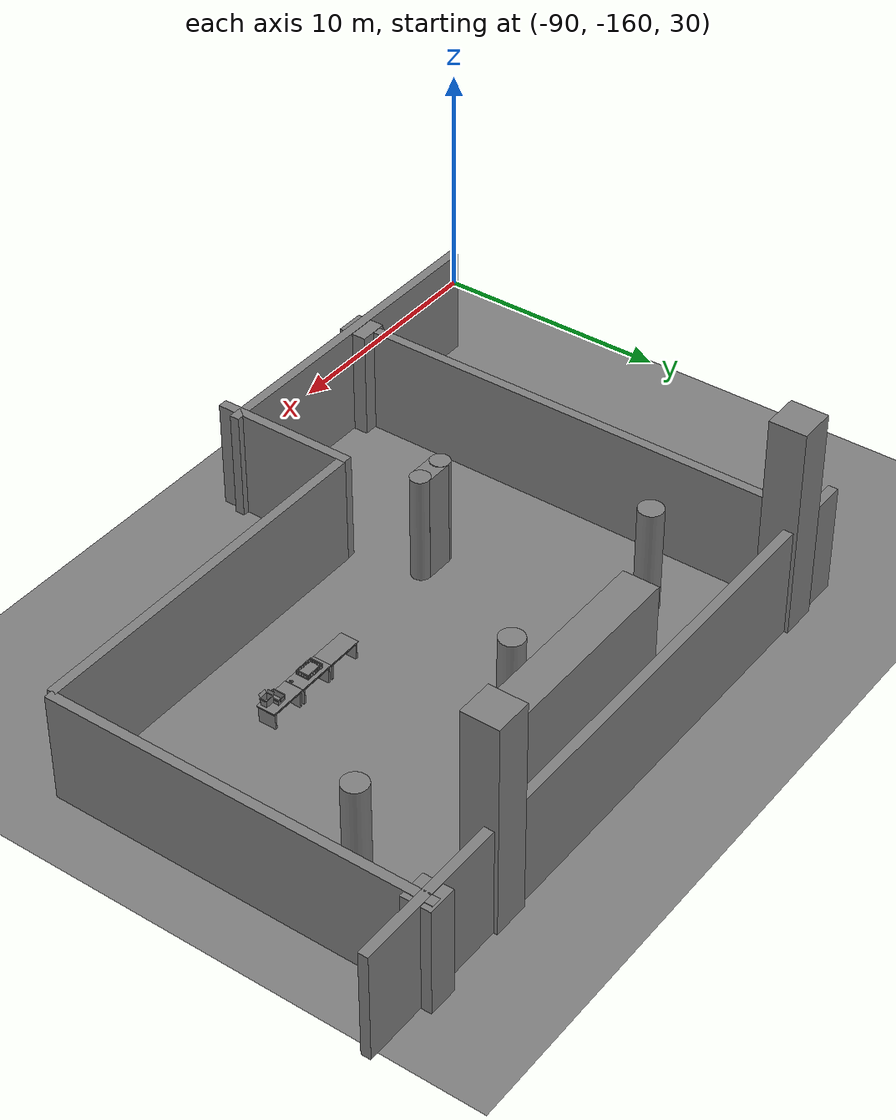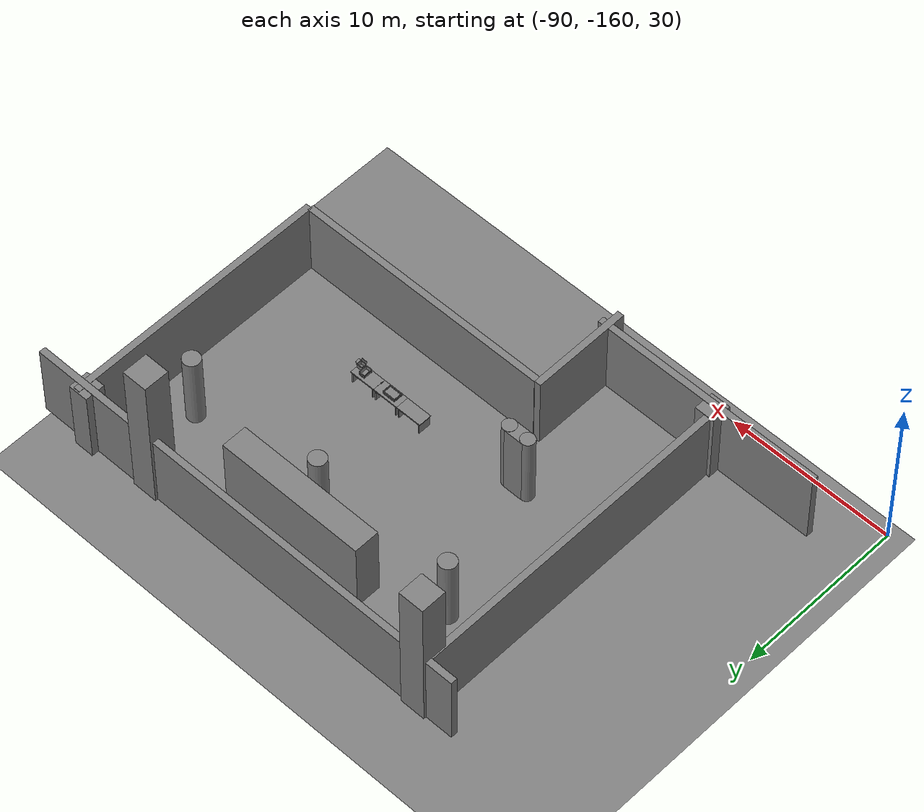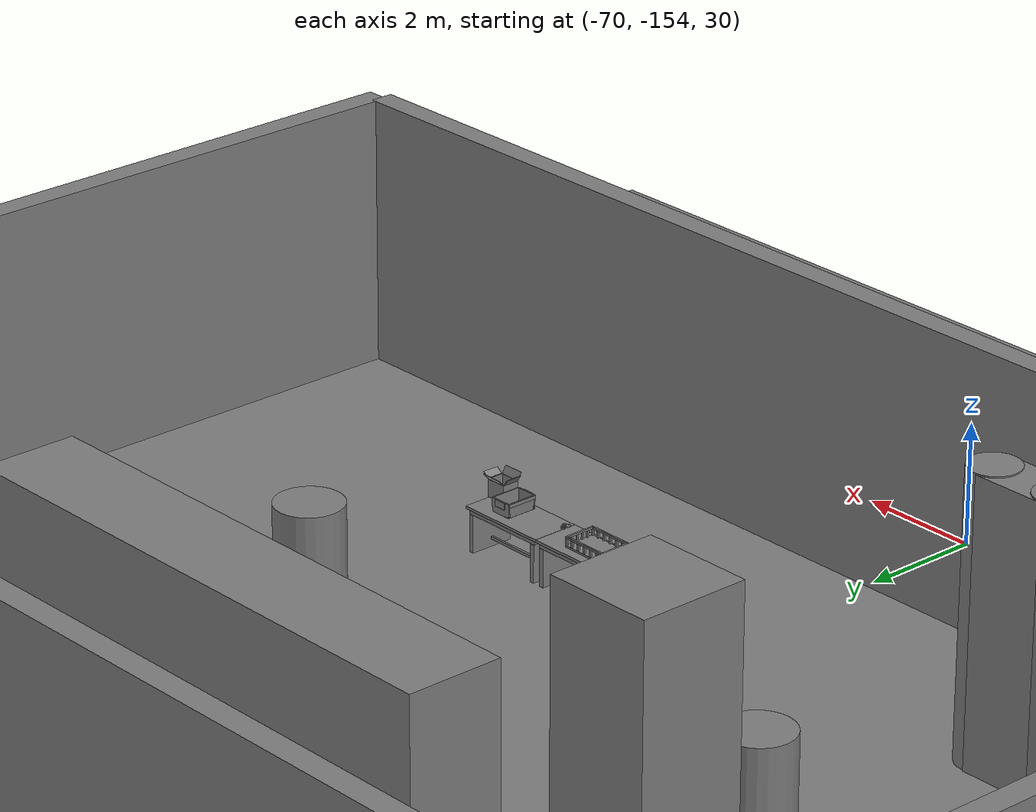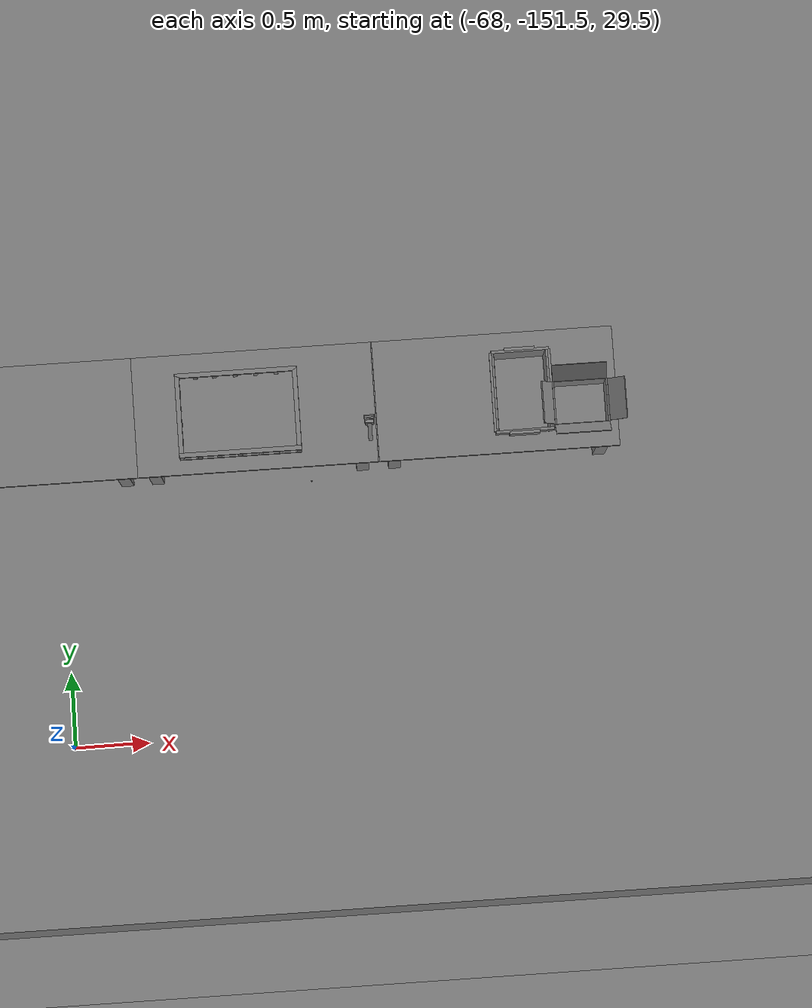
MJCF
<mujoco>
    <option gravity="0.000000000 0.000000000 -9.810000420" timestep="0.0049999999" integrator="implicitfast" density="1.225" viscosity="1.8000001e-05" noslip_iterations="10" iterations="100" sdf_iterations="50">
        <flag multiccd="disable"/>
    </option>
    <size memory="1000M"/>
    <compiler coordinate="local"/>
    <worldbody>
        <light cutoff="30" pos="0 1 1" dir="0 -1 -2"/>
        <light cutoff="30" pos="0 -1 1" dir="0 1 -2"/>
        <body pos="-64.866622925 -149.383972168 30.183746338" euler="89.999992371 89.999946594 0.000000000" name="openloong_gripper_2f85_fix_base_usda_bluebox_01">
            <geom contype="1" conaffinity="1" density="1000" type="box" material="" rgba="0.500000000 0.500000000 0.500000000 1.000000000" solimp="0.899999976 0.949999988 0.001000000" friction="1.000000000 0.005000000 0.000100000" solref="0.020000000 1.000000000" margin="0" condim="3" group="0" pos="0.276596069 0.187225342 0.000061035" quat="0.707107008 0.000077501 0.707106471 0.000077456" size="0.100000001 0.057999998 0.010000000" name="openloong_gripper_2f85_fix_base_usda_geom_D55464F8_B42E_4DD7_9A80_7C5A70E4F762"/>
            <geom contype="1" conaffinity="1" density="1000" type="box" material="" rgba="0.500000000 0.500000000 0.500000000 1.000000000" solimp="0.899999976 0.949999988 0.001000000" friction="1.000000000 0.005000000 0.000100000" solref="0.020000000 1.000000000" margin="0" condim="3" group="0" pos="0.000000000 0.002883911 0.000000000" quat="1.000000000 0.000000000 0.000000000 0.000000000" size="0.254000008 0.003000000 0.172000006" name="openloong_gripper_2f85_fix_base_usda_geom_A8E9A286_5311_42AB_9C6D_8F8D9F61EFE3"/>
            <geom contype="1" conaffinity="1" density="1000" type="box" material="" rgba="0.500000000 0.500000000 0.500000000 1.000000000" solimp="0.899999976 0.949999988 0.001000000" friction="1.000000000 0.005000000 0.000100000" solref="0.020000000 1.000000000" margin="0" condim="3" group="0" pos="0.000015259 0.124874115 0.173477173" quat="0.999796450 0.020176515 -0.000000015 0.000000030" size="0.259999990 0.119999997 0.007000000" name="openloong_gripper_2f85_fix_base_usda_geom_E7F49556_614F_460F_9426_FCA1651FFE17"/>
            <geom contype="1" conaffinity="1" density="1000" type="box" material="" rgba="0.500000000 0.500000000 0.500000000 1.000000000" solimp="0.899999976 0.949999988 0.001000000" friction="1.000000000 0.005000000 0.000100000" solref="0.020000000 1.000000000" margin="0" condim="3" group="0" pos="0.000015259 0.124874115 -0.173477173" quat="0.999796450 -0.020176545 -0.000000015 0.000000000" size="0.259999990 0.119999997 0.007000000" name="openloong_gripper_2f85_fix_base_usda_geom_E99658C8_55AB_4A8D_A0B0_DF1033A60979"/>
            <geom contype="1" conaffinity="1" density="1000" type="box" material="" rgba="0.500000000 0.500000000 0.500000000 1.000000000" solimp="0.899999976 0.949999988 0.001000000" friction="1.000000000 0.005000000 0.000100000" solref="0.020000000 1.000000000" margin="0" condim="3" group="0" pos="0.000015259 0.214012146 0.188980103" quat="0.999913096 0.013176724 0.000000015 0.000000000" size="0.259999990 0.029999999 0.012500000" name="openloong_gripper_2f85_fix_base_usda_geom_8E90815A_A157_4F8D_8FB4_0CE4535657F7"/>
            <geom contype="1" conaffinity="1" density="1000" type="box" material="" rgba="0.500000000 0.500000000 0.500000000 1.000000000" solimp="0.899999976 0.949999988 0.001000000" friction="1.000000000 0.005000000 0.000100000" solref="0.020000000 1.000000000" margin="0" condim="3" group="0" pos="-0.258346558 0.125289917 0.001876831" quat="0.702796996 -0.020792052 0.710783184 0.020769238" size="0.189999998 0.119999997 0.009000000" name="openloong_gripper_2f85_fix_base_usda_geom_13AD3ADA_5454_4CBF_BDD2_CA04A44A2F6C"/>
            <geom contype="1" conaffinity="1" density="1000" type="box" material="" rgba="0.500000000 0.500000000 0.500000000 1.000000000" solimp="0.899999976 0.949999988 0.001000000" friction="1.000000000 0.005000000 0.000100000" solref="0.020000000 1.000000000" margin="0" condim="3" group="0" pos="0.000015259 0.214012146 -0.188980103" quat="0.999913096 -0.013176769 0.000000030 0.000000015" size="0.259999990 0.029999999 0.012500000" name="openloong_gripper_2f85_fix_base_usda_geom_CB40C04E_1157_4F86_B61C_FF2EAEBB301B"/>
            <geom contype="1" conaffinity="1" density="1000" type="box" material="" rgba="0.500000000 0.500000000 0.500000000 1.000000000" solimp="0.899999976 0.949999988 0.001000000" friction="1.000000000 0.005000000 0.000100000" solref="0.020000000 1.000000000" margin="0" condim="3" group="0" pos="-0.276596069 0.187225342 0.000061035" quat="0.707106650 0.000077441 0.707106709 0.000077456" size="0.100000001 0.057999998 0.010000000" name="openloong_gripper_2f85_fix_base_usda_geom_B62C7DF3_ED66_4077_9C20_9BBE61BB4A9F"/>
            <geom contype="1" conaffinity="1" density="1000" type="box" material="" rgba="0.500000000 0.500000000 0.500000000 1.000000000" solimp="0.899999976 0.949999988 0.001000000" friction="1.000000000 0.005000000 0.000100000" solref="0.020000000 1.000000000" margin="0" condim="3" group="0" pos="0.258346558 0.125289917 0.001876831" quat="0.702851534 0.018856451 0.710823834 -0.019329429" size="0.189999998 0.119999997 0.009000000" name="openloong_gripper_2f85_fix_base_usda_geom_3CD40A93_B1F8_46CF_89C6_9D3F86E70846"/>
            <freejoint name="openloong_gripper_2f85_fix_base_usda_bluebox_01_joint"/>
            <site size="0.005000000 0.005000000 0.005000000" rgba="0.500000000 0.500000000 0.500000000 1.000000000" pos="0.000000000 0.000000000 0.000000000" quat="0.999961913 0.008726534 0.000000000 0.000000000" group="0" type="sphere" name="openloong_gripper_2f85_fix_base_usda_bluebox_01site"/>
        </body>
        <body pos="-64.496299744 -149.491867065 30.235729218" euler="0.000000000 0.000000000 89.999946594" name="openloong_gripper_2f85_fix_base_usda_cardboardbox_01">
            <geom contype="1" conaffinity="1" density="1000" type="box" material="" rgba="0.500000000 0.500000000 0.500000000 1.000000000" solimp="0.899999976 0.949999988 0.001000000" friction="1.000000000 0.005000000 0.000100000" solref="0.020000000 1.000000000" margin="0" condim="3" group="0" pos="-0.003166199 -0.004086494 0.005052090" quat="1.000000000 0.000000000 0.000000000 0.000000000" size="0.142499998 0.177500010 0.005000000" name="openloong_gripper_2f85_fix_base_usda_geom_914A3423_E27F_4C62_9BE5_00091866D39A"/>
            <geom contype="1" conaffinity="1" density="1000" type="box" material="" rgba="0.500000000 0.500000000 0.500000000 1.000000000" solimp="0.899999976 0.949999988 0.001000000" friction="1.000000000 0.005000000 0.000100000" solref="0.020000000 1.000000000" margin="0" condim="3" group="0" pos="-0.003166199 0.170316696 0.150570869" quat="1.000000000 0.000000000 0.000000000 0.000000000" size="0.142499998 0.005000000 0.149999991" name="openloong_gripper_2f85_fix_base_usda_geom_658D47ED_3EC3_4163_B670_2F43E6C50860"/>
            <geom contype="1" conaffinity="1" density="1000" type="box" material="" rgba="0.500000000 0.500000000 0.500000000 1.000000000" solimp="0.899999976 0.949999988 0.001000000" friction="1.000000000 0.005000000 0.000100000" solref="0.020000000 1.000000000" margin="0" condim="3" group="0" pos="-0.147399902 -0.005307198 0.150570869" quat="1.000000000 0.000000000 0.000000000 0.000000000" size="0.005000000 0.177500010 0.149999991" name="openloong_gripper_2f85_fix_base_usda_geom_499891BE_BB28_4CE9_AC12_B15E03D42430"/>
            <geom contype="1" conaffinity="1" density="1000" type="box" material="" rgba="0.500000000 0.500000000 0.500000000 1.000000000" solimp="0.899999976 0.949999988 0.001000000" friction="1.000000000 0.005000000 0.000100000" solref="0.020000000 1.000000000" margin="0" condim="3" group="0" pos="0.140275955 -0.005307198 0.150570869" quat="1.000000000 0.000000000 0.000000000 0.000000000" size="0.005000000 0.177500010 0.149999991" name="openloong_gripper_2f85_fix_base_usda_geom_71B0EFBE_BBF3_4404_B3E9_7FFCE11FEE38"/>
            <geom contype="1" conaffinity="1" density="1000" type="box" material="" rgba="0.500000000 0.500000000 0.500000000 1.000000000" solimp="0.899999976 0.949999988 0.001000000" friction="1.000000000 0.005000000 0.000100000" solref="0.020000000 1.000000000" margin="0" condim="3" group="0" pos="-0.003166199 -0.181550980 0.150570869" quat="1.000000000 0.000000000 0.000000000 0.000000000" size="0.142499998 0.005000000 0.149999991" name="openloong_gripper_2f85_fix_base_usda_geom_3FBD1737_DB4E_4047_BE68_8884157B1DAB"/>
            <freejoint name="openloong_gripper_2f85_fix_base_usda_cardboardbox_01_joint"/>
            <site size="0.005000000 0.005000000 0.005000000" rgba="0.500000000 0.500000000 0.500000000 1.000000000" pos="0.000000000 0.000000000 0.000000000" quat="0.999961913 0.008726535 0.000000000 0.000000000" group="0" type="sphere" name="openloong_gripper_2f85_fix_base_usda_site_A00803BF_DD68_4FB3_B1DF_19358AC83A8C"/>
            <body pos="0.139160156 -0.004048347 0.301930904" euler="-179.999954224 49.383502960 179.999954224" name="openloong_gripper_2f85_fix_base_usda_A1_006">
                <geom contype="1" conaffinity="1" density="1000" type="box" material="" rgba="0.500000000 0.500000000 0.500000000 1.000000000" solimp="0.899999976 0.949999988 0.001000000" friction="1.000000000 0.005000000 0.000100000" solref="0.020000000 1.000000000" margin="0" condim="3" group="0" pos="-0.071587563 0.000009537 0.001745224" quat="0.999999881 0.000000000 0.000000000 0.000000000" size="0.071249999 0.179999992 0.002500000" name="openloong_gripper_2f85_fix_base_usda_geom_4D7A4D15_2FC4_48B7_9427_A954EA44D663"/>
                <joint armature="0" stiffness="0.07" damping="0.0099999998" axis="0.000000 1.000000 0.000000" type="hinge" name="openloong_gripper_2f85_fix_base_usda_A1_006"/>
            </body>
            <body pos="-0.145902634 -0.004086494 0.301938057" euler="-180.000000000 -60.000011444 -180.000000000" name="openloong_gripper_2f85_fix_base_usda_A2_006">
                <geom contype="1" conaffinity="1" density="1000" type="box" material="" rgba="0.500000000 0.500000000 0.500000000 1.000000000" solimp="0.899999976 0.949999988 0.001000000" friction="1.000000000 0.005000000 0.000100000" solref="0.020000000 1.000000000" margin="0" condim="3" group="0" pos="0.071268082 0.000009537 0.002717972" quat="0.000002921 0.000000000 -0.000000030 0.999999881" size="0.071249999 0.179999992 0.002500000" name="openloong_gripper_2f85_fix_base_usda_geom_CBBE5F88_E4F8_4162_B7D7_187EE2B574E2"/>
                <joint armature="0" stiffness="0.07" damping="0.0099999998" axis="0.000000 1.000000 0.000000" type="hinge" name="openloong_gripper_2f85_fix_base_usda_A2_006"/>
            </body>
            <body pos="-0.003385544 0.175991058 0.301930904" euler="-125.858116150 -0.000004561 0.000002331" name="openloong_gripper_2f85_fix_base_usda_B2_006">
                <geom contype="1" conaffinity="1" density="1000" type="box" material="" rgba="0.500000000 0.500000000 0.500000000 1.000000000" solimp="0.899999976 0.949999988 0.001000000" friction="1.000000000 0.005000000 0.000100000" solref="0.020000000 1.000000000" margin="0" condim="3" group="0" pos="0.000009537 -0.070939064 -0.002470016" quat="0.999614120 0.027776197 -0.000000015 0.000000030" size="0.137500003 0.064999998 0.005000000" name="openloong_gripper_2f85_fix_base_usda_geom_0B4EDC47_1339_4CD7_8D59_6C8559D4E795"/>
                <joint armature="0" stiffness="0.07" damping="0.0099999998" axis="1.000000 0.000000 0.000000" type="hinge" name="openloong_gripper_2f85_fix_base_usda_B2_006"/>
            </body>
            <body pos="-0.003385544 -0.184140205 0.301938057" euler="147.805557251 0.000000000 0.000000000" name="openloong_gripper_2f85_fix_base_usda_B1_006">
                <geom contype="1" conaffinity="1" density="1000" type="box" material="" rgba="0.500000000 0.500000000 0.500000000 1.000000000" solimp="0.899999976 0.949999988 0.001000000" friction="1.000000000 0.005000000 0.000100000" solref="0.020000000 1.000000000" margin="0" condim="3" group="0" pos="-0.000028610 0.070202351 -0.002703667" quat="0.999614179 -0.027776167 0.000000000 0.000000000" size="0.137500003 0.064999998 0.005000000" name="openloong_gripper_2f85_fix_base_usda_geom_5040E841_177A_4A2C_AEB9_19767141D0EB"/>
                <joint armature="0" stiffness="0.07" damping="0.0099999998" axis="1.000000 0.000000 0.000000" type="hinge" name="openloong_gripper_2f85_fix_base_usda_B1_006"/>
            </body>
        </body>
        <body pos="-65.882858276 -149.481979370 30.229999542" euler="-64.487716675 0.000000000 0.000000000" name="openloong_gripper_2f85_fix_base_usda_Barcode">
            <geom contype="1" conaffinity="1" density="1000" type="box" material="" rgba="0.500000000 0.500000000 0.500000000 1.000000000" solimp="0.899999976 0.949999988 0.001000000" friction="1.000000000 0.005000000 0.000100000" solref="0.020000000 1.000000000" margin="0" condim="3" group="0" pos="0.000000000 0.013038635 0.001419067" quat="0.000000000 0.000000000 0.000000000 1.000000119" size="0.034000002 0.010000000 0.017999999" name="openloong_gripper_2f85_fix_base_usda_geom_2219D622_F764_4B10_AC81_EF6DFB9325D5"/>
            <geom contype="1" conaffinity="1" density="1000" type="box" material="" rgba="0.500000000 0.500000000 0.500000000 1.000000000" solimp="0.899999976 0.949999988 0.001000000" friction="1.000000000 0.005000000 0.000100000" solref="0.020000000 1.000000000" margin="0" condim="3" group="0" pos="0.000000000 -0.035301208 -0.007095337" quat="0.000000000 0.000000000 -0.043619365 0.999048233" size="0.028999999 0.010000000 0.020000000" name="openloong_gripper_2f85_fix_base_usda_geom_45B8F0EA_BF5C_4CFE_8F8E_15C5F4462D2E"/>
            <geom contype="1" conaffinity="1" density="1000" type="box" material="" rgba="0.500000000 0.500000000 0.500000000 1.000000000" solimp="0.899999976 0.949999988 0.001000000" friction="1.000000000 0.005000000 0.000100000" solref="0.020000000 1.000000000" margin="0" condim="3" group="0" pos="0.000000000 -0.043411255 -0.011749268" quat="0.922262907 0.386563420 0.000000000 0.000000000" size="0.026000001 0.010000000 0.020000000" name="openloong_gripper_2f85_fix_base_usda_geom_BB47DD40_1762_486F_8482_F0B86712BCCD"/>
            <geom contype="1" conaffinity="1" density="1000" type="box" material="" rgba="0.500000000 0.500000000 0.500000000 1.000000000" solimp="0.899999976 0.949999988 0.001000000" friction="1.000000000 0.005000000 0.000100000" solref="0.020000000 1.000000000" margin="0" condim="3" group="0" pos="0.000000000 -0.016967773 -0.031860352" quat="0.000000000 0.000000000 0.000000000 1.000000119" size="0.008000000 0.010000000 0.013000000" name="openloong_gripper_2f85_fix_base_usda_geom_13C0E79C_35CE_48C6_8E30_B419BAFBE7A8"/>
            <geom contype="1" conaffinity="1" density="1000" type="box" material="" rgba="0.500000000 0.500000000 0.500000000 1.000000000" solimp="0.899999976 0.949999988 0.001000000" friction="1.000000000 0.005000000 0.000100000" solref="0.020000000 1.000000000" margin="0" condim="3" group="0" pos="0.000000000 -0.001869202 0.000312805" quat="0.953716993 0.300705761 0.000000000 0.000000000" size="0.032000002 0.010000000 0.018999999" name="openloong_gripper_2f85_fix_base_usda_geom_80130874_317A_44D2_B02A_9F1AADFA368D"/>
            <geom contype="1" conaffinity="1" density="1000" type="box" material="" rgba="0.500000000 0.500000000 0.500000000 1.000000000" solimp="0.899999976 0.949999988 0.001000000" friction="1.000000000 0.005000000 0.000100000" solref="0.020000000 1.000000000" margin="0" condim="3" group="0" pos="0.000000000 -0.019531250 -0.003173828" quat="0.953716993 0.300705761 0.000000000 0.000000000" size="0.030999999 0.010000000 0.020000000" name="openloong_gripper_2f85_fix_base_usda_geom_DD4F37AC_33A4_41B0_B5C2_B25521CAE9B6"/>
            <geom contype="1" conaffinity="1" density="1000" type="box" material="" rgba="0.500000000 0.500000000 0.500000000 1.000000000" solimp="0.899999976 0.949999988 0.001000000" friction="1.000000000 0.005000000 0.000100000" solref="0.020000000 1.000000000" margin="0" condim="3" group="0" pos="0.000000000 -0.035301208 -0.007095337" quat="0.953716993 0.300705761 0.000000000 0.000000000" size="0.028999999 0.010000000 0.020000000" name="openloong_gripper_2f85_fix_base_usda_geom_729A4605_C08A_4380_AF52_9668A33BBDDA"/>
            <geom contype="1" conaffinity="1" density="1000" type="box" material="" rgba="0.500000000 0.500000000 0.500000000 1.000000000" solimp="0.899999976 0.949999988 0.001000000" friction="1.000000000 0.005000000 0.000100000" solref="0.020000000 1.000000000" margin="0" condim="3" group="0" pos="0.000000000 -0.042617798 -0.071121216" quat="0.000000000 0.000000000 0.000000000 1.000000119" size="0.013000000 0.021000000 0.059999999" name="openloong_gripper_2f85_fix_base_usda_geom_BCEE6B9F_9CC7_48BE_B70C_12B026134304"/>
            <freejoint name="openloong_gripper_2f85_fix_base_usda_Barcode_joint"/>
            <site size="0.005000000 0.005000000 0.005000000" rgba="0.500000000 0.500000000 0.500000000 1.000000000" pos="0.000000000 0.000000000 0.000000000" quat="1.000000000 0.000000000 0.000000000 0.000000000" group="0" type="sphere" name="openloong_gripper_2f85_fix_base_usda_Barcode_site"/>
        </body>
        <body pos="-66.745018005 -149.392349243 30.184000015" euler="0.000000000 0.000000000 89.999946594" name="[22329606617452]_Basket_01">
            <geom contype="1" conaffinity="1" density="1000" type="box" material="" rgba="0.500000000 0.500000000 0.500000000 1.000000000" solimp="0.899999976 0.949999988 0.001000000" friction="1.000000000 0.005000000 0.000100000" solref="0.020000000 1.000000000" margin="0" condim="3" group="0" pos="-0.052425385 0.389207840 0.089787483" quat="0.707107008 0.000000000 0.000000000 0.707106411" size="0.014249999 0.014249999 0.059999999" name="[22329606617452]_geom_BD7AB28B_EE43_430D_8852_3D97A5D71674"/>
            <geom contype="1" conaffinity="1" density="1000" type="box" material="" rgba="0.500000000 0.500000000 0.500000000 1.000000000" solimp="0.899999976 0.949999988 0.001000000" friction="1.000000000 0.005000000 0.000100000" solref="0.020000000 1.000000000" margin="0" condim="3" group="0" pos="0.264015198 -0.133043289 0.089787483" quat="0.707107008 0.000000000 0.000000000 0.707106411" size="0.014249999 0.014249999 0.059999999" name="[22329606617452]_geom_1A9B2435_5F23_4083_8F04_30DFEB77A243"/>
            <geom contype="1" conaffinity="1" density="1000" type="box" material="" rgba="0.500000000 0.500000000 0.500000000 1.000000000" solimp="0.899999976 0.949999988 0.001000000" friction="1.000000000 0.005000000 0.000100000" solref="0.020000000 1.000000000" margin="0" condim="3" group="0" pos="-0.264015198 -0.265548706 0.089793205" quat="0.707107008 0.000000000 0.000000000 0.707106411" size="0.014249999 0.014249999 0.059999999" name="[22329606617452]_geom_D86300E6_DB4B_4E17_889D_C14A9A0F8206"/>
            <geom contype="1" conaffinity="1" density="1000" type="box" material="" rgba="0.500000000 0.500000000 0.500000000 1.000000000" solimp="0.899999976 0.949999988 0.001000000" friction="1.000000000 0.005000000 0.000100000" solref="0.020000000 1.000000000" margin="0" condim="3" group="0" pos="-0.160263062 -0.389322281 0.089793205" quat="0.707107008 0.000000000 0.000000000 0.707106411" size="0.014249999 0.014249999 0.059999999" name="[22329606617452]_geom_248111AE_D671_450B_B412_1B4A8CC8C213"/>
            <geom contype="1" conaffinity="1" density="1000" type="box" material="" rgba="0.500000000 0.500000000 0.500000000 1.000000000" solimp="0.899999976 0.949999988 0.001000000" friction="1.000000000 0.005000000 0.000100000" solref="0.020000000 1.000000000" margin="0" condim="3" group="0" pos="0.162265778 -0.389322281 0.089787483" quat="0.707107008 0.000000000 0.000000000 0.707106411" size="0.014249999 0.014249999 0.059999999" name="[22329606617452]_geom_2BFB9B64_0F80_4B22_A87F_D89CFBA853A8"/>
            <geom contype="1" conaffinity="1" density="1000" type="box" material="" rgba="0.500000000 0.500000000 0.500000000 1.000000000" solimp="0.899999976 0.949999988 0.001000000" friction="1.000000000 0.005000000 0.000100000" solref="0.020000000 1.000000000" margin="0" condim="3" group="0" pos="0.264015198 0.389207840 0.089787483" quat="0.707107008 0.000000000 0.000000000 0.707106411" size="0.014249999 0.014249999 0.059999999" name="[22329606617452]_geom_0D708F7E_AD53_4E7E_A236_6099DF5CBBC2"/>
            <geom contype="1" conaffinity="1" density="1000" type="box" material="" rgba="0.500000000 0.500000000 0.500000000 1.000000000" solimp="0.899999976 0.949999988 0.001000000" friction="1.000000000 0.005000000 0.000100000" solref="0.020000000 1.000000000" margin="0" condim="3" group="0" pos="-0.264015198 -0.133043289 0.089793205" quat="0.707107008 0.000000000 0.000000000 0.707106411" size="0.014249999 0.014249999 0.059999999" name="[22329606617452]_geom_8564D059_248F_47DA_8A5C_6FD35C7D451C"/>
            <geom contype="1" conaffinity="1" density="1000" type="box" material="" rgba="0.500000000 0.500000000 0.500000000 1.000000000" solimp="0.899999976 0.949999988 0.001000000" friction="1.000000000 0.005000000 0.000100000" solref="0.020000000 1.000000000" margin="0" condim="3" group="0" pos="-0.264026642 0.269256592 0.089793205" quat="0.707107008 0.000000000 0.000000000 0.707106411" size="0.014249999 0.014249999 0.059999999" name="[22329606617452]_geom_A03A54B2_4303_4A05_A2C8_6DF989D5C7D0"/>
            <geom contype="1" conaffinity="1" density="1000" type="box" material="" rgba="0.500000000 0.500000000 0.500000000 1.000000000" solimp="0.899999976 0.949999988 0.001000000" friction="1.000000000 0.005000000 0.000100000" solref="0.020000000 1.000000000" margin="0" condim="3" group="0" pos="0.054462433 0.389207840 0.089787483" quat="0.707107008 0.000000000 0.000000000 0.707106411" size="0.014249999 0.014249999 0.059999999" name="[22329606617452]_geom_F59C702B_0C0B_4513_8826_AF892A1067E0"/>
            <geom contype="1" conaffinity="1" density="1000" type="box" material="" rgba="0.500000000 0.500000000 0.500000000 1.000000000" solimp="0.899999976 0.949999988 0.001000000" friction="1.000000000 0.005000000 0.000100000" solref="0.020000000 1.000000000" margin="0" condim="3" group="0" pos="0.054462433 -0.389322281 0.089787483" quat="0.707107008 0.000000000 0.000000000 0.707106411" size="0.014249999 0.014249999 0.059999999" name="[22329606617452]_geom_CA83ED62_2A6E_4F03_9F9C_AAEF696DBFB5"/>
            <geom contype="1" conaffinity="1" density="1000" type="box" material="" rgba="0.500000000 0.500000000 0.500000000 1.000000000" solimp="0.899999976 0.949999988 0.001000000" friction="1.000000000 0.005000000 0.000100000" solref="0.020000000 1.000000000" margin="0" condim="3" group="0" pos="0.264015198 0.269256592 0.089793205" quat="0.707107008 0.000000000 0.000000000 0.707106411" size="0.014249999 0.014249999 0.059999999" name="[22329606617452]_geom_D6634CBB_8B5E_450F_BEF8_746C8450CD07"/>
            <geom contype="1" conaffinity="1" density="1000" type="box" material="" rgba="0.500000000 0.500000000 0.500000000 1.000000000" solimp="0.899999976 0.949999988 0.001000000" friction="1.000000000 0.005000000 0.000100000" solref="0.020000000 1.000000000" margin="0" condim="3" group="0" pos="0.264015198 -0.389322281 0.089787483" quat="0.707107008 0.000000000 0.000000000 0.707106411" size="0.014249999 0.014249999 0.059999999" name="[22329606617452]_geom_635E04C3_A142_4AAF_941F_0B86EF42A8E3"/>
            <geom contype="1" conaffinity="1" density="1000" type="box" material="" rgba="0.500000000 0.500000000 0.500000000 1.000000000" solimp="0.899999976 0.949999988 0.001000000" friction="1.000000000 0.005000000 0.000100000" solref="0.020000000 1.000000000" margin="0" condim="3" group="0" pos="0.000000000 0.000000000 0.015998840" quat="0.707107008 0.000000000 0.000000000 0.707106411" size="0.403499991 0.279000014 0.015750000" name="[22329606617452]_geom_6B3005DB_4023_400F_9289_3F9DBD62DD31"/>
            <geom contype="1" conaffinity="1" density="1000" type="box" material="" rgba="0.500000000 0.500000000 0.500000000 1.000000000" solimp="0.899999976 0.949999988 0.001000000" friction="1.000000000 0.005000000 0.000100000" solref="0.020000000 1.000000000" margin="0" condim="3" group="0" pos="0.000000000 -0.389476776 0.163619041" quat="0.707107008 0.000000000 0.000000000 0.707106411" size="0.015000000 0.277500004 0.015750000" name="[22329606617452]_geom_4C9B8D3E_C6ED_4688_818B_02BBEF625053"/>
            <geom contype="1" conaffinity="1" density="1000" type="box" material="" rgba="0.500000000 0.500000000 0.500000000 1.000000000" solimp="0.899999976 0.949999988 0.001000000" friction="1.000000000 0.005000000 0.000100000" solref="0.020000000 1.000000000" margin="0" condim="3" group="0" pos="0.162265778 0.389207840 0.089787483" quat="0.707107008 0.000000000 0.000000000 0.707106411" size="0.014249999 0.014249999 0.059999999" name="[22329606617452]_geom_429B4128_597D_40DA_B179_41A068880F82"/>
            <geom contype="1" conaffinity="1" density="1000" type="box" material="" rgba="0.500000000 0.500000000 0.500000000 1.000000000" solimp="0.899999976 0.949999988 0.001000000" friction="1.000000000 0.005000000 0.000100000" solref="0.020000000 1.000000000" margin="0" condim="3" group="0" pos="0.000000000 0.389471054 0.163619041" quat="0.707107008 0.000000000 0.000000000 0.707106411" size="0.015000000 0.277500004 0.015750000" name="[22329606617452]_geom_2CDA3FC6_C983_4C52_B67B_6FD09EE22C56"/>
            <geom contype="1" conaffinity="1" density="1000" type="box" material="" rgba="0.500000000 0.500000000 0.500000000 1.000000000" solimp="0.899999976 0.949999988 0.001000000" friction="1.000000000 0.005000000 0.000100000" solref="0.020000000 1.000000000" margin="0" condim="3" group="0" pos="-0.263511658 0.000000000 0.163619041" quat="0.707107008 0.000000000 0.000000000 0.707106411" size="0.403499991 0.015000000 0.015750000" name="[22329606617452]_geom_BADB1D0C_D985_4E33_8DBC_745FD8A2C441"/>
            <geom contype="1" conaffinity="1" density="1000" type="box" material="" rgba="0.500000000 0.500000000 0.500000000 1.000000000" solimp="0.899999976 0.949999988 0.001000000" friction="1.000000000 0.005000000 0.000100000" solref="0.020000000 1.000000000" margin="0" condim="3" group="0" pos="-0.264015198 0.141334534 0.089793205" quat="0.707107008 0.000000000 0.000000000 0.707106411" size="0.014249999 0.014249999 0.059999999" name="[22329606617452]_geom_4D3A614B_613E_4328_8F8E_0C3F8316CA06"/>
            <geom contype="1" conaffinity="1" density="1000" type="box" material="" rgba="0.500000000 0.500000000 0.500000000 1.000000000" solimp="0.899999976 0.949999988 0.001000000" friction="1.000000000 0.005000000 0.000100000" solref="0.020000000 1.000000000" margin="0" condim="3" group="0" pos="0.264015198 -0.265548706 0.089787483" quat="0.707107008 0.000000000 0.000000000 0.707106411" size="0.014249999 0.014249999 0.059999999" name="[22329606617452]_geom_2E40FB11_DC0C_4FBC_B031_599FB23A1297"/>
            <geom contype="1" conaffinity="1" density="1000" type="box" material="" rgba="0.500000000 0.500000000 0.500000000 1.000000000" solimp="0.899999976 0.949999988 0.001000000" friction="1.000000000 0.005000000 0.000100000" solref="0.020000000 1.000000000" margin="0" condim="3" group="0" pos="-0.160263062 0.389207840 0.089787483" quat="0.707107008 0.000000000 0.000000000 0.707106411" size="0.014249999 0.014249999 0.059999999" name="[22329606617452]_geom_F527201A_A526_48F1_BA5E_9679E5EB3FE9"/>
            <geom contype="1" conaffinity="1" density="1000" type="box" material="" rgba="0.500000000 0.500000000 0.500000000 1.000000000" solimp="0.899999976 0.949999988 0.001000000" friction="1.000000000 0.005000000 0.000100000" solref="0.020000000 1.000000000" margin="0" condim="3" group="0" pos="-0.052425385 -0.389322281 0.089787483" quat="0.707107008 0.000000000 0.000000000 0.707106411" size="0.014249999 0.014249999 0.059999999" name="[22329606617452]_geom_F8034FD0_307E_4BCA_861E_9F3C150C9A12"/>
            <geom contype="1" conaffinity="1" density="1000" type="box" material="" rgba="0.500000000 0.500000000 0.500000000 1.000000000" solimp="0.899999976 0.949999988 0.001000000" friction="1.000000000 0.005000000 0.000100000" solref="0.020000000 1.000000000" margin="0" condim="3" group="0" pos="-0.264026642 -0.389322281 0.089793205" quat="0.707107008 0.000000000 0.000000000 0.707106411" size="0.014249999 0.014249999 0.059999999" name="[22329606617452]_geom_A915CBA0_C167_4C98_BB0A_FC18EAA55DB9"/>
            <geom contype="1" conaffinity="1" density="1000" type="box" material="" rgba="0.500000000 0.500000000 0.500000000 1.000000000" solimp="0.899999976 0.949999988 0.001000000" friction="1.000000000 0.005000000 0.000100000" solref="0.020000000 1.000000000" margin="0" condim="3" group="0" pos="0.264015198 0.141334534 0.089787483" quat="0.707107008 0.000000000 0.000000000 0.707106411" size="0.014249999 0.014249999 0.059999999" name="[22329606617452]_geom_74D23F49_EAD6_4021_BD01_EB4EA98788EE"/>
            <geom contype="1" conaffinity="1" density="1000" type="box" material="" rgba="0.500000000 0.500000000 0.500000000 1.000000000" solimp="0.899999976 0.949999988 0.001000000" friction="1.000000000 0.005000000 0.000100000" solref="0.020000000 1.000000000" margin="0" condim="3" group="0" pos="-0.264015198 0.389207840 0.089793205" quat="0.707107008 0.000000000 0.000000000 0.707106411" size="0.014249999 0.014249999 0.059999999" name="[22329606617452]_geom_0969DBA9_A891_4282_9221_2F6602F03E78"/>
            <geom contype="1" conaffinity="1" density="1000" type="box" material="" rgba="0.500000000 0.500000000 0.500000000 1.000000000" solimp="0.899999976 0.949999988 0.001000000" friction="1.000000000 0.005000000 0.000100000" solref="0.020000000 1.000000000" margin="0" condim="3" group="0" pos="0.264015198 0.004480362 0.089787483" quat="0.707107008 0.000000000 0.000000000 0.707106411" size="0.014249999 0.014249999 0.059999999" name="[22329606617452]_geom_067F7E23_786F_4EBF_8935_9A5D96DF1F80"/>
            <geom contype="1" conaffinity="1" density="1000" type="box" material="" rgba="0.500000000 0.500000000 0.500000000 1.000000000" solimp="0.899999976 0.949999988 0.001000000" friction="1.000000000 0.005000000 0.000100000" solref="0.020000000 1.000000000" margin="0" condim="3" group="0" pos="0.263694763 -0.000011444 0.163619041" quat="0.707107008 0.000000000 0.000000000 0.707106411" size="0.403499991 0.015000000 0.015750000" name="[22329606617452]_geom_44D75A6C_01C5_4B6C_957A_4D9BBA5228F6"/>
            <geom contype="1" conaffinity="1" density="1000" type="box" material="" rgba="0.500000000 0.500000000 0.500000000 1.000000000" solimp="0.899999976 0.949999988 0.001000000" friction="1.000000000 0.005000000 0.000100000" solref="0.020000000 1.000000000" margin="0" condim="3" group="0" pos="-0.264015198 0.004480362 0.089793205" quat="0.707107008 0.000000000 0.000000000 0.707106411" size="0.014249999 0.014249999 0.059999999" name="[22329606617452]_geom_8D165057_FD32_4FDF_88C6_DC22E9BA1DCA"/>
            <freejoint name="[22329606617452]_joint_D7D6256E_26AE_4C8F_89DD_6ABFA04B5584"/>
        </body>
        <body pos="0.000000000 0.000000000 0.000000000" euler="0.000000000 0.000000000 0.000000000" name="Static Objects_Static Objects">
            <geom contype="1" conaffinity="1" density="1000" type="box" material="" rgba="0.500000000 0.500000000 0.500000000 1.000000000" solimp="0.899999976 0.949999988 0.001000000" friction="1.000000000 0.005000000 0.000100000" solref="0.020000000 1.000000000" margin="0" condim="3" group="0" pos="-67.544113159 -149.365814209 29.727830887" quat="0.500000417 0.499999970 0.499999553 0.499999970" size="0.381000012 0.319999993 0.041000001" name="Static Objects_geom_EB2AAB62_B475_47D3_A581_53BD618E00C4"/>
            <geom contype="1" conaffinity="1" density="1000" type="box" material="" rgba="0.500000000 0.500000000 0.500000000 1.000000000" solimp="0.899999976 0.949999988 0.001000000" friction="1.000000000 0.005000000 0.000100000" solref="0.020000000 1.000000000" margin="0" condim="3" group="0" pos="-68.239501953 -149.365814209 30.086868286" quat="0.500000417 0.499999970 0.499999553 0.499999970" size="0.370999992 0.039500002 0.745000005" name="Static Objects_geom_C93CDCCE_EAC5_46A5_BD48_F8832289E004"/>
            <geom contype="1" conaffinity="1" density="1000" type="box" material="" rgba="0.500000000 0.500000000 0.500000000 1.000000000" solimp="0.899999976 0.949999988 0.001000000" friction="1.000000000 0.005000000 0.000100000" solref="0.020000000 1.000000000" margin="0" condim="3" group="0" pos="-68.239501953 -149.365814209 30.147235870" quat="0.500000417 0.499999970 0.499999553 0.499999970" size="0.400000006 0.022000000 0.800000012" name="Static Objects_geom_BD143960_4F6F_4C25_B6FC_5EEEFB9BAE81"/>
            <geom contype="1" conaffinity="1" density="1000" type="box" material="" rgba="0.500000000 0.500000000 0.500000000 1.000000000" solimp="0.899999976 0.949999988 0.001000000" friction="1.000000000 0.005000000 0.000100000" solref="0.020000000 1.000000000" margin="0" condim="3" group="0" pos="-68.934890747 -149.365814209 29.727830887" quat="0.500000417 0.499999970 0.499999553 0.499999970" size="0.381000012 0.319999993 0.041000001" name="Static Objects_geom_7427EA14_13F8_4E74_9C90_C43DCD4CF00B"/>
            <geom contype="1" conaffinity="1" density="1000" type="box" material="" rgba="0.500000000 0.500000000 0.500000000 1.000000000" solimp="0.899999976 0.949999988 0.001000000" friction="1.000000000 0.005000000 0.000100000" solref="0.020000000 1.000000000" margin="0" condim="3" group="0" pos="-68.239501953 -149.365814209 29.561563492" quat="0.500000417 0.499999970 0.499999553 0.499999970" size="0.020000000 0.022000000 0.660000026" name="Static Objects_geom_1EE55E03_5323_40E0_B98F_F4B60BA8B509"/>
            <geom contype="1" conaffinity="1" density="1000" type="box" material="" rgba="0.500000000 0.500000000 0.500000000 1.000000000" solimp="0.899999976 0.949999988 0.001000000" friction="1.000000000 0.005000000 0.000100000" solref="0.020000000 1.000000000" margin="0" condim="3" group="0" pos="-65.945671082 -149.365814209 29.727830887" quat="0.500000417 0.499999970 0.499999553 0.499999970" size="0.381000012 0.319999993 0.041000001" name="Static Objects_geom_2BF1A12D_4800_44BB_9312_FF5B70116450"/>
            <geom contype="1" conaffinity="1" density="1000" type="box" material="" rgba="0.500000000 0.500000000 0.500000000 1.000000000" solimp="0.899999976 0.949999988 0.001000000" friction="1.000000000 0.005000000 0.000100000" solref="0.020000000 1.000000000" margin="0" condim="3" group="0" pos="-66.641059875 -149.365814209 30.086868286" quat="0.500000417 0.499999970 0.499999553 0.499999970" size="0.370999992 0.039500002 0.745000005" name="Static Objects_geom_BD553984_4EB7_4557_B68B_C7E7DD5084DC"/>
            <geom contype="1" conaffinity="1" density="1000" type="box" material="" rgba="0.500000000 0.500000000 0.500000000 1.000000000" solimp="0.899999976 0.949999988 0.001000000" friction="1.000000000 0.005000000 0.000100000" solref="0.020000000 1.000000000" margin="0" condim="3" group="0" pos="-66.641059875 -149.365814209 30.147235870" quat="0.500000417 0.499999970 0.499999553 0.499999970" size="0.400000006 0.022000000 0.800000012" name="Static Objects_geom_D1E80926_BC74_446B_8229_F0D90DEB5051"/>
            <geom contype="1" conaffinity="1" density="1000" type="box" material="" rgba="0.500000000 0.500000000 0.500000000 1.000000000" solimp="0.899999976 0.949999988 0.001000000" friction="1.000000000 0.005000000 0.000100000" solref="0.020000000 1.000000000" margin="0" condim="3" group="0" pos="-67.336448669 -149.365814209 29.727830887" quat="0.500000417 0.499999970 0.499999553 0.499999970" size="0.381000012 0.319999993 0.041000001" name="Static Objects_geom_EB49600B_3621_4E74_80F5_416416B69E53"/>
            <geom contype="1" conaffinity="1" density="1000" type="box" material="" rgba="0.500000000 0.500000000 0.500000000 1.000000000" solimp="0.899999976 0.949999988 0.001000000" friction="1.000000000 0.005000000 0.000100000" solref="0.020000000 1.000000000" margin="0" condim="3" group="0" pos="-66.641059875 -149.365814209 29.561563492" quat="0.500000417 0.499999970 0.499999553 0.499999970" size="0.020000000 0.022000000 0.660000026" name="Static Objects_geom_AA9D5D4C_87A7_4EA0_AF0D_59E19B32D899"/>
            <geom contype="1" conaffinity="1" density="1000" type="box" material="" rgba="0.500000000 0.500000000 0.500000000 1.000000000" solimp="0.899999976 0.949999988 0.001000000" friction="1.000000000 0.005000000 0.000100000" solref="0.020000000 1.000000000" margin="0" condim="3" group="0" pos="-64.338577271 -149.365814209 29.727830887" quat="0.500000417 0.499999970 0.499999553 0.499999970" size="0.381000012 0.319999993 0.041000001" name="Static Objects_geom_3A5B5F55_D00D_4AB6_AE32_4889693B0855"/>
            <geom contype="1" conaffinity="1" density="1000" type="box" material="" rgba="0.500000000 0.500000000 0.500000000 1.000000000" solimp="0.899999976 0.949999988 0.001000000" friction="1.000000000 0.005000000 0.000100000" solref="0.020000000 1.000000000" margin="0" condim="3" group="0" pos="-65.033966064 -149.365814209 30.086868286" quat="0.500000417 0.499999970 0.499999553 0.499999970" size="0.370999992 0.039500002 0.745000005" name="Static Objects_geom_8D875DA1_F919_4CBD_ABEB_CEBC71E25A64"/>
            <geom contype="1" conaffinity="1" density="1000" type="box" material="" rgba="0.500000000 0.500000000 0.500000000 1.000000000" solimp="0.899999976 0.949999988 0.001000000" friction="1.000000000 0.005000000 0.000100000" solref="0.020000000 1.000000000" margin="0" condim="3" group="0" pos="-65.033966064 -149.365814209 30.147235870" quat="0.500000417 0.499999970 0.499999553 0.499999970" size="0.400000006 0.022000000 0.800000012" name="Static Objects_geom_195CDF93_D186_4A07_AB0C_2018D63B0B6E"/>
            <geom contype="1" conaffinity="1" density="1000" type="box" material="" rgba="0.500000000 0.500000000 0.500000000 1.000000000" solimp="0.899999976 0.949999988 0.001000000" friction="1.000000000 0.005000000 0.000100000" solref="0.020000000 1.000000000" margin="0" condim="3" group="0" pos="-65.729354858 -149.365814209 29.727830887" quat="0.500000417 0.499999970 0.499999553 0.499999970" size="0.381000012 0.319999993 0.041000001" name="Static Objects_geom_3816B087_65DE_44D1_9184_966922167D6B"/>
            <geom contype="1" conaffinity="1" density="1000" type="box" material="" rgba="0.500000000 0.500000000 0.500000000 1.000000000" solimp="0.899999976 0.949999988 0.001000000" friction="1.000000000 0.005000000 0.000100000" solref="0.020000000 1.000000000" margin="0" condim="3" group="0" pos="-65.033966064 -149.365814209 29.561563492" quat="0.500000417 0.499999970 0.499999553 0.499999970" size="0.020000000 0.022000000 0.660000026" name="Static Objects_geom_598579CA_609B_409F_9398_BBC8CECEFC55"/>
            <geom contype="1" conaffinity="1" density="1000" type="box" material="" rgba="0.500000000 0.500000000 0.500000000 1.000000000" solimp="0.899999976 0.949999988 0.001000000" friction="1.000000000 0.005000000 0.000100000" solref="0.020000000 1.000000000" margin="0" condim="3" group="0" pos="-61.754566193 -137.853729248 33.906845093" quat="0.707107067 0.000000000 0.000000000 0.707106471" size="0.759999990 0.759999990 4.500000000" name="Static Objects_geom_2E44889B_7FD3_4C40_8853_620E93F5B8C7"/>
            <geom contype="1" conaffinity="1" density="1000" type="box" material="" rgba="0.500000000 0.500000000 0.500000000 1.000000000" solimp="0.899999976 0.949999988 0.001000000" friction="1.000000000 0.005000000 0.000100000" solref="0.020000000 1.000000000" margin="0" condim="3" group="0" pos="-57.511135101 -144.927108765 31.707921982" quat="1.000000000 0.000000000 0.000000000 0.000000000" size="0.200000003 8.000000000 2.299999952" name="Static Objects_geom_803EFB8E_A1EF_4A82_AE56_F7E24AE8BC26"/>
            <geom contype="1" conaffinity="1" density="1000" type="box" material="" rgba="0.500000000 0.500000000 0.500000000 1.000000000" solimp="0.899999976 0.949999988 0.001000000" friction="1.000000000 0.005000000 0.000100000" solref="0.020000000 1.000000000" margin="0" condim="3" group="0" pos="-80.517646790 -157.574050903 31.688196182" quat="0.707107067 0.000000000 0.000000000 0.707106471" size="0.600000024 0.600000024 2.299999952" name="Static Objects_geom_EDD5FDAA_95D9_4AC9_A2D8_357CC9DCD3E9"/>
            <geom contype="1" conaffinity="1" density="1000" type="box" material="" rgba="0.500000000 0.500000000 0.500000000 1.000000000" solimp="0.899999976 0.949999988 0.001000000" friction="1.000000000 0.005000000 0.000100000" solref="0.020000000 1.000000000" margin="0" condim="3" group="0" pos="-80.711044312 -147.414932251 31.666158676" quat="1.000000000 0.000000000 0.000000000 0.000000000" size="0.200000003 10.000000000 2.299999952" name="Static Objects_geom_987EF1C4_0871_4D16_88B1_FA2D4721B3B6"/>
            <geom contype="1" conaffinity="1" density="1000" type="box" material="" rgba="0.500000000 0.500000000 0.500000000 1.000000000" solimp="0.899999976 0.949999988 0.001000000" friction="1.000000000 0.005000000 0.000100000" solref="0.020000000 1.000000000" margin="0" condim="3" group="0" pos="-57.687217712 -137.434692383 31.688196182" quat="0.707107067 0.000000000 0.000000000 0.707106471" size="0.600000024 0.600000024 2.299999952" name="Static Objects_geom_28A5F4C4_721C_40F4_8B49_BBA51D60014D"/>
            <geom contype="1" conaffinity="1" density="1000" type="box" material="" rgba="0.500000000 0.500000000 0.500000000 1.000000000" solimp="0.899999976 0.949999988 0.001000000" friction="1.000000000 0.005000000 0.000100000" solref="0.020000000 1.000000000" margin="0" condim="3" group="0" pos="-69.537033081 -140.263229370 31.714921951" quat="0.707107067 0.000000000 0.000000000 0.707106471" size="0.759999990 4.500000000 2.299999952" name="Static Objects_geom_BA8F5F62_ED3C_4C9F_967D_A2BFFFFBE9D4"/>
            <geom contype="1" conaffinity="1" density="1000" type="box" material="" rgba="0.500000000 0.500000000 0.500000000 1.000000000" solimp="0.899999976 0.949999988 0.001000000" friction="1.000000000 0.005000000 0.000100000" solref="0.020000000 1.000000000" margin="0" condim="3" group="0" pos="-80.073638916 -137.853713989 33.906845093" quat="0.707107067 0.000000000 0.000000000 0.707106471" size="0.759999990 0.759999990 4.500000000" name="Static Objects_geom_C09522E5_CFC6_4CED_B482_BB0E1FBE3B33"/>
            <geom contype="1" conaffinity="1" density="1000" type="box" material="" rgba="0.500000000 0.500000000 0.500000000 1.000000000" solimp="0.899999976 0.949999988 0.001000000" friction="1.000000000 0.005000000 0.000100000" solref="0.020000000 1.000000000" margin="0" condim="3" group="0" pos="-73.406707764 -155.734664917 31.707921982" quat="1.000000000 0.000000000 0.000000000 0.000000000" size="0.200000003 3.000000000 2.299999952" name="Static Objects_geom_B8039ADB_282C_4C55_AB4C_528D5CF426E0"/>
            <geom contype="1" conaffinity="1" density="1000" type="box" material="" rgba="0.500000000 0.500000000 0.500000000 1.000000000" solimp="0.899999976 0.949999988 0.001000000" friction="1.000000000 0.005000000 0.000100000" solref="0.020000000 1.000000000" margin="0" condim="3" group="0" pos="-68.497543335 -137.448257446 31.707921982" quat="0.707107067 0.000000000 0.000000000 0.707106471" size="0.200000003 14.000000000 2.299999952" name="Static Objects_geom_CADBD599_C0C8_4845_8517_9B8F93842FE9"/>
            <geom contype="1" conaffinity="1" density="1000" type="cylinder" material="" rgba="0.500000000 0.500000000 0.500000000 1.000000000" solimp="0.899999976 0.949999988 0.001000000" friction="1.000000000 0.005000000 0.000100000" solref="0.020000000 1.000000000" margin="0" condim="3" group="0" pos="-68.868522644 -142.134506226 31.711090088" quat="0.707107067 0.000000000 0.000000000 0.707106471" size="0.509999990 2.299999952 1.000000000" name="Static Objects_geom_264199BE_A8B5_4494_AFC1_E473583159B0"/>
            <geom contype="1" conaffinity="1" density="1000" type="plane" material="" rgba="0.500000000 0.500000000 0.500000000 1.000000000" solimp="0.899999976 0.949999988 0.001000000" friction="1.000000000 0.005000000 0.000100000" solref="0.020000000 1.000000000" margin="0" condim="3" group="0" pos="-72.873703003 -147.131927490 29.409669876" quat="1.000000000 0.000000000 0.000000000 0.000000000" size="18.000000000 14.000000000 1.000000000" name="Static Objects_geom_84DF35F2_F117_46F2_A762_21BBD391E990"/>
            <geom contype="1" conaffinity="1" density="1000" type="box" material="" rgba="0.500000000 0.500000000 0.500000000 1.000000000" solimp="0.899999976 0.949999988 0.001000000" friction="1.000000000 0.005000000 0.000100000" solref="0.020000000 1.000000000" margin="0" condim="3" group="0" pos="-79.943580627 -157.782272339 31.707921982" quat="0.707107067 0.000000000 0.000000000 0.707106471" size="0.200000003 7.000000000 2.299999952" name="Static Objects_geom_636F5BFF_9BF7_463F_B8D6_8F49DCBB3D6F"/>
            <geom contype="1" conaffinity="1" density="1000" type="box" material="" rgba="0.500000000 0.500000000 0.500000000 1.000000000" solimp="0.899999976 0.949999988 0.001000000" friction="1.000000000 0.005000000 0.000100000" solref="0.020000000 1.000000000" margin="0" condim="3" group="0" pos="-65.421028137 -152.903442383 31.707921982" quat="0.707107067 0.000000000 0.000000000 0.707106471" size="0.200000003 7.800000191 2.299999952" name="Static Objects_geom_ABC404E5_40B2_4B61_A99D_268150959EE7"/>
            <geom contype="1" conaffinity="1" density="1000" type="box" material="" rgba="0.500000000 0.500000000 0.500000000 1.000000000" solimp="0.899999976 0.949999988 0.001000000" friction="1.000000000 0.005000000 0.000100000" solref="0.020000000 1.000000000" margin="0" condim="3" group="0" pos="-74.776908875 -149.964416504 31.688196182" quat="1.000000000 0.000000000 0.000000000 0.000000000" size="0.600000024 0.409999996 2.299999952" name="Static Objects_geom_5D998E22_6723_41E4_B3AF_C9A9C7A7EDD5"/>
            <geom contype="1" conaffinity="1" density="1000" type="cylinder" material="" rgba="0.500000000 0.500000000 0.500000000 1.000000000" solimp="0.899999976 0.949999988 0.001000000" friction="1.000000000 0.005000000 0.000100000" solref="0.020000000 1.000000000" margin="0" condim="3" group="0" pos="-60.161884308 -142.134506226 31.711090088" quat="0.707107067 0.000000000 0.000000000 0.707106471" size="0.509999990 2.299999952 1.000000000" name="Static Objects_geom_76F52009_27B4_4CB3_884B_8C5B0AC3EC33"/>
            <geom contype="1" conaffinity="1" density="1000" type="cylinder" material="" rgba="0.500000000 0.500000000 0.500000000 1.000000000" solimp="0.899999976 0.949999988 0.001000000" friction="1.000000000 0.005000000 0.000100000" solref="0.020000000 1.000000000" margin="0" condim="3" group="0" pos="-75.382453918 -149.963455200 31.711090088" quat="0.707107067 0.000000000 0.000000000 0.707106471" size="0.409999996 2.299999952 1.000000000" name="Static Objects_geom_F3339E9D_90FD_4E32_AB79_0B687EFECA6D"/>
            <geom contype="1" conaffinity="1" density="1000" type="cylinder" material="" rgba="0.500000000 0.500000000 0.500000000 1.000000000" solimp="0.899999976 0.949999988 0.001000000" friction="1.000000000 0.005000000 0.000100000" solref="0.020000000 1.000000000" margin="0" condim="3" group="0" pos="-74.154960632 -149.963455200 31.711090088" quat="0.707107067 0.000000000 0.000000000 0.707106471" size="0.409999996 2.299999952 1.000000000" name="Static Objects_geom_F4A1524B_2B0F_45D6_B8C3_548B48AD68A8"/>
            <geom contype="1" conaffinity="1" density="1000" type="cylinder" material="" rgba="0.500000000 0.500000000 0.500000000 1.000000000" solimp="0.899999976 0.949999988 0.001000000" friction="1.000000000 0.005000000 0.000100000" solref="0.020000000 1.000000000" margin="0" condim="3" group="0" pos="-77.566612244 -142.134506226 31.711090088" quat="0.707107067 0.000000000 0.000000000 0.707106471" size="0.509999990 2.299999952 1.000000000" name="Static Objects_geom_31FF1917_DEB0_43A5_AE30_58FDDEE531F5"/>
        </body>
        <body pos="-66.291030884 -149.869689941 29.018842697" euler="0.000000000 0.000000000 89.999946594" mocap="true" name="openloong_gripper_2f85_fix_base_usda_leftHandMocap"/>
        <body pos="-66.291030884 -149.869689941 29.018842697" euler="0.000000000 0.000000000 89.999946594" mocap="true" name="openloong_gripper_2f85_fix_base_usda_rightHandMocap"/>
        <body pos="-66.291030884 -149.869689941 30.218843460" euler="0.000000000 0.000000000 89.999946594" name="openloong_gripper_2f85_fix_base_usda_base_link">
            <geom contype="1" conaffinity="1" density="1000" type="mesh" material="" rgba="0.783999979 0.783999979 0.783999979 1.000000000" solimp="0.899999976 0.949999988 0.001000000" friction="1.000000000 0.005000000 0.000100000" solref="0.020000000 1.000000000" margin="0" condim="3" group="3" mesh="base_link" pos="0.000000000 0.000000000 0.000000000" quat="1.000000000 0.000000000 0.000000000 0.000000000" size="1.000000000 1.000000000 1.000000000" name="openloong_gripper_2f85_fix_base_usda__geom_7_A9CCD81D_3A2A_4C95_B881_8B52DDF9E48D"/>
            <site size="0.005000000 0.005000000 0.005000000" rgba="0.500000000 0.500000000 0.500000000 1.000000000" pos="0.000000000 0.000000000 0.000000000" quat="1.000000000 0.000000000 0.000000000 0.000000000" group="0" type="sphere" name="openloong_gripper_2f85_fix_base_usda_imu"/>
            <inertial mass="22.447001" pos="-0.005664100 -0.001336700 0.238289997" diaginertia="0.374352545 0.277180195 0.220617250" quat="0.999247074 0.035235517 -0.015086859 0.006023135"/>
            <body pos="0.000000000 0.000000000 0.299997330" euler="0.000000000 0.000000000 0.000000000" name="openloong_gripper_2f85_fix_base_usda_dummy_body">
                <geom contype="1" conaffinity="1" density="1000" type="sphere" material="" rgba="0.783999979 0.783999979 0.783999979 1.000000000" solimp="0.899999976 0.949999988 0.001000000" friction="1.000000000 0.005000000 0.000100000" solref="0.020000000 1.000000000" margin="0" condim="3" group="3" pos="0.000000000 0.000000000 0.000000000" quat="1.000000000 0.000000000 0.000000000 0.000000000" size="0.010000000 0.000000000 0.000000000" name="openloong_gripper_2f85_fix_base_usda__geom_8_2A9C5F97_80F0_44D9_884D_ACD4D31E2B99"/>
                <joint armature="0.0099999998" stiffness="0" damping="0.1" axis="0.000000 0.000000 1.000000" type="hinge" name="openloong_gripper_2f85_fix_base_usda_dummy_joint"/>
                <site size="0.010000000 0.005000000 0.005000000" rgba="0.500000000 0.500000000 0.500000000 1.000000000" pos="0.000000000 0.000000000 0.000000000" quat="1.000000000 0.000000000 0.000000000 0.000000000" group="3" type="sphere" name="openloong_gripper_2f85_fix_base_usda_dummy_site"/>
            </body>
            <body pos="0.009002686 0.000000000 0.406400681" euler="0.000000000 0.000000000 0.000000000" name="openloong_gripper_2f85_fix_base_usda_Link_head_yaw">
                <geom contype="1" conaffinity="1" density="1000" type="mesh" material="" rgba="0.783999979 0.783999979 0.783999979 1.000000000" solimp="0.899999976 0.949999988 0.001000000" friction="1.000000000 0.005000000 0.000100000" solref="0.020000000 1.000000000" margin="0" condim="3" group="3" mesh="Link_head_yaw" pos="0.000000000 0.000000000 0.000000000" quat="1.000000000 0.000000000 0.000000000 0.000000000" size="1.000000000 1.000000000 1.000000000" name="openloong_gripper_2f85_fix_base_usda__geom_10_43D0BC48_7069_4EC9_B186_15F983B2DA5A"/>
                <inertial mass="0.84249002" pos="0.000000000 -0.002081400 0.044801001" diaginertia="0.000700588 0.000629000 0.000553812" quat="0.706933022 -0.015675601 0.015677100 0.706933022"/>
                <body pos="0.000000000 -0.034599304 0.048500061" euler="0.000000000 0.000000000 0.000000000" name="openloong_gripper_2f85_fix_base_usda_Link_head_pitch">
                    <geom contype="1" conaffinity="1" density="1000" type="mesh" material="" rgba="0.783999979 0.783999979 0.783999979 1.000000000" solimp="0.899999976 0.949999988 0.001000000" friction="1.000000000 0.005000000 0.000100000" solref="0.020000000 1.000000000" margin="0" condim="3" group="3" mesh="Link_head_pitch" pos="0.000000000 0.000000000 0.000000000" quat="1.000000000 0.000000000 0.000000000 0.000000000" size="1.000000000 1.000000000 1.000000000" name="openloong_gripper_2f85_fix_base_usda__geom_12_A15B4681_F149_40CE_9F89_62C40AAA681F"/>
                    <inertial mass="1.3943" pos="0.020569000 0.033004001 0.125000000" diaginertia="0.006381400 0.006289940 0.004481460" quat="0.973390222 0.008406822 0.228157058 0.019624906"/>
                    <body pos="0.000000000 0.029998779 0.000000000" euler="0.000000000 0.000000000 0.000000000" name="openloong_gripper_2f85_fix_base_usda_neck_center_body">
                        <site size="0.010000000 0.005000000 0.005000000" rgba="0.500000000 0.500000000 0.500000000 1.000000000" pos="0.000000000 0.000000000 0.000000000" quat="1.000000000 0.000000000 0.000000000 0.000000000" group="3" type="sphere" name="openloong_gripper_2f85_fix_base_usda_neck_center_site"/>
                        <body pos="0.020004272 0.000000000 0.149999619" euler="-0.000002229 39.998176575 -90.000205994" name="openloong_gripper_2f85_fix_base_usda_camera_head">
                            <site size="0.010000000 0.005000000 0.005000000" rgba="0.500000000 0.500000000 0.500000000 1.000000000" pos="0.000000000 0.000000000 0.000000000" quat="1.000000000 0.000000000 0.000000000 0.000000000" group="3" type="sphere" name="openloong_gripper_2f85_fix_base_usda_camera_head_site"/>
                        </body>
                    </body>
                </body>
            </body>
            <body pos="0.003997803 -0.161598206 0.392200470" euler="0.000000000 0.000000000 0.000000000" name="openloong_gripper_2f85_fix_base_usda_Link_arm_r_01">
                <geom contype="1" conaffinity="1" density="1000" type="mesh" material="" rgba="0.783999979 0.783999979 0.783999979 1.000000000" solimp="0.899999976 0.949999988 0.001000000" friction="1.000000000 0.005000000 0.000100000" solref="0.020000000 1.000000000" margin="0" condim="3" group="3" mesh="Link_arm_r_01" pos="0.000000000 0.000000000 0.000000000" quat="1.000000000 0.000000000 0.000000000 0.000000000" size="1.000000000 1.000000000 1.000000000" name="openloong_gripper_2f85_fix_base_usda__geom_14_53CAA9F6_9C8C_4606_9076_F1D66AEA601C"/>
                <joint armature="0.0099999998" stiffness="0" damping="1" axis="0.000000 -1.000000 0.000000" limited="true" range="-170.000015259 170.000015259" type="hinge" name="openloong_gripper_2f85_fix_base_usda_J_arm_r_01"/>
                <inertial mass="0.75641" pos="0.004494600 -0.038293999 -0.000001874" diaginertia="0.000842990 0.000803050 0.000587120" quat="-0.000163502 0.707098067 0.000812463 0.707115054"/>
                <body pos="-0.041992188 -0.041000366 0.000000000" euler="0.000000000 0.000000000 0.000000000" name="openloong_gripper_2f85_fix_base_usda_Link_arm_r_02">
                    <geom contype="1" conaffinity="1" density="1000" type="mesh" material="" rgba="0.783999979 0.783999979 0.783999979 1.000000000" solimp="0.899999976 0.949999988 0.001000000" friction="1.000000000 0.005000000 0.000100000" solref="0.020000000 1.000000000" margin="0" condim="3" group="3" mesh="Link_arm_r_02" pos="0.000000000 0.000000000 0.000000000" quat="1.000000000 0.000000000 0.000000000 0.000000000" size="1.000000000 1.000000000 1.000000000" name="openloong_gripper_2f85_fix_base_usda__geom_16_5B9429AA_A725_4691_837F_1DD23F490994"/>
                    <joint armature="0.0099999998" stiffness="0" damping="1" axis="-1.000000 0.000000 0.000000" limited="true" range="-105.000244141 105.000244141" type="hinge" name="openloong_gripper_2f85_fix_base_usda_J_arm_r_02"/>
                    <inertial mass="0.98500001" pos="0.041999999 -0.067430697 0.000000000" diaginertia="0.002262690 0.001730990 0.001154020" quat="0.500000000 0.500000000 -0.500000000 0.500000000"/>
                    <body pos="0.041992188 -0.122596741 0.000000000" euler="0.000000000 0.000000000 0.000000000" name="openloong_gripper_2f85_fix_base_usda_Link_arm_r_03">
                        <geom contype="1" conaffinity="1" density="1000" type="mesh" material="" rgba="0.783999979 0.783999979 0.783999979 1.000000000" solimp="0.899999976 0.949999988 0.001000000" friction="1.000000000 0.005000000 0.000100000" solref="0.020000000 1.000000000" margin="0" condim="3" group="3" mesh="Link_arm_r_03" pos="0.000000000 0.000000000 0.000000000" quat="1.000000000 0.000000000 0.000000000 0.000000000" size="1.000000000 1.000000000 1.000000000" name="openloong_gripper_2f85_fix_base_usda__geom_18_21A3CDD3_E5E1_4B7A_8DD5_908C7BC8742C"/>
                        <joint armature="0.0099999998" stiffness="0" damping="1" axis="0.000000 -1.000000 0.000000" limited="true" range="-170.000015259 170.000015259" type="hinge" name="openloong_gripper_2f85_fix_base_usda_J_arm_r_03"/>
                        <inertial mass="0.95899999" pos="-0.001413580 -0.164663002 0.020757901" diaginertia="0.002101340 0.002064590 0.000754802" quat="0.560480952 0.454391927 -0.443732947 0.531497955"/>
                        <body pos="0.035293579 -0.177406311 0.023998260" euler="0.000000000 0.000000000 0.000000000" name="openloong_gripper_2f85_fix_base_usda_Link_arm_r_04">
                            <geom contype="1" conaffinity="1" density="1000" type="mesh" material="" rgba="0.783999979 0.783999979 0.783999979 1.000000000" solimp="0.899999976 0.949999988 0.001000000" friction="1.000000000 0.005000000 0.000100000" solref="0.020000000 1.000000000" margin="0" condim="3" group="3" mesh="Link_arm_r_04" pos="0.000000000 0.000000000 0.000000000" quat="1.000000000 0.000000000 0.000000000 0.000000000" size="1.000000000 1.000000000 1.000000000" name="openloong_gripper_2f85_fix_base_usda__geom_20_4F4CCF4C_6C0F_4BBE_AB1A_70888B8DA5D6"/>
                            <joint armature="0.0099999998" stiffness="0" damping="1" axis="-1.000000 0.000000 0.000000" limited="true" range="0.000000000 170.000015259" type="hinge" name="openloong_gripper_2f85_fix_base_usda_J_arm_r_04"/>
                            <inertial mass="0.60000002" pos="-0.038727000 -0.060766999 -0.021003000" diaginertia="0.001092610 0.000712422 0.000645102" quat="0.327701002 0.632602990 -0.467366993 0.523443997"/>
                            <body pos="-0.035293579 -0.103492737 -0.023998260" euler="0.000000000 0.000000000 0.000000000" name="openloong_gripper_2f85_fix_base_usda_Link_arm_r_05">
                                <geom contype="1" conaffinity="1" density="1000" type="mesh" material="" rgba="0.783999979 0.783999979 0.783999979 1.000000000" solimp="0.899999976 0.949999988 0.001000000" friction="1.000000000 0.005000000 0.000100000" solref="0.020000000 1.000000000" margin="0" condim="3" group="3" mesh="Link_arm_r_05" pos="0.000000000 0.000000000 0.000000000" quat="1.000000000 0.000000000 0.000000000 0.000000000" size="1.000000000 1.000000000 1.000000000" name="openloong_gripper_2f85_fix_base_usda__geom_22_974ECE58_CE15_4326_9365_78E72F05AD33"/>
                                <joint armature="0.0099999998" stiffness="0" damping="1" axis="0.000000 -1.000000 0.000000" limited="true" range="-170.000015259 170.000015259" type="hinge" name="openloong_gripper_2f85_fix_base_usda_J_arm_r_05"/>
                                <inertial mass="0.68976003" pos="0.000032712 -0.068658002 -0.000111780" diaginertia="0.002522510 0.002411100 0.000448695" quat="0.707660973 0.706543028 -0.002603360 0.002470550"/>
                                <body pos="-0.026489258 -0.196502686 0.000000000" euler="0.000000000 0.000000000 0.000000000" name="openloong_gripper_2f85_fix_base_usda_Link_arm_r_06">
                                    <geom contype="1" conaffinity="1" density="1000" type="mesh" material="" rgba="0.783999979 0.783999979 0.783999979 1.000000000" solimp="0.899999976 0.949999988 0.001000000" friction="1.000000000 0.005000000 0.000100000" solref="0.020000000 1.000000000" margin="0" condim="3" group="3" mesh="Link_arm_r_06" pos="0.000000000 0.000000000 0.000000000" quat="1.000000000 0.000000000 0.000000000 0.000000000" size="1.000000000 1.000000000 1.000000000" name="openloong_gripper_2f85_fix_base_usda__geom_24_5DB78CEA_CB8C_483B_9D25_45B0238425F1"/>
                                    <joint armature="0.0099999998" stiffness="0" damping="1" axis="1.000000 0.000000 0.000000" limited="true" range="-105.000244141 105.000244141" type="hinge" name="openloong_gripper_2f85_fix_base_usda_J_arm_r_06"/>
                                    <inertial mass="0.28" pos="0.026078001 -0.000000896 0.001663700" diaginertia="0.000156930 0.000145601 0.000104979" quat="0.707080841 0.001851080 0.001883810 0.707127810"/>
                                    <body pos="0.026489258 0.000000000 0.031799316" euler="0.000000000 0.000000000 0.000000000" name="openloong_gripper_2f85_fix_base_usda_Link_arm_r_07">
                                        <geom contype="1" conaffinity="1" density="1000" type="mesh" material="" rgba="0.783999979 0.783999979 0.783999979 1.000000000" solimp="0.899999976 0.949999988 0.001000000" friction="1.000000000 0.005000000 0.000100000" solref="0.020000000 1.000000000" margin="0" condim="3" group="3" mesh="Link_arm_r_07" pos="0.000000000 0.000000000 0.000000000" quat="1.000000000 0.000000000 0.000000000 0.000000000" size="1.000000000 1.000000000 1.000000000" name="openloong_gripper_2f85_fix_base_usda__geom_26_6D27D619_7E03_4C60_8A45_7AD677F61526"/>
                                        <joint armature="0.0099999998" stiffness="0" damping="1" axis="0.000000 0.000000 1.000000" limited="true" range="-60.000133514 60.000133514" type="hinge" name="openloong_gripper_2f85_fix_base_usda_J_arm_r_07"/>
                                        <inertial mass="0.61353999" pos="-0.007859000 -0.158170000 -0.027736001" diaginertia="0.003037610 0.002570910 0.000729379" quat="0.427542925 0.443532884 -0.553093910 0.560867906"/>
                                        <body pos="0.000000000 0.286994934 -0.270000458" euler="150.000350952 -0.000001649 -0.000000442" name="openloong_gripper_2f85_fix_base_usda_camera_wrist_r">
                                            <site size="0.010000000 0.005000000 0.005000000" rgba="0.500000000 0.500000000 0.500000000 1.000000000" pos="0.000000000 0.000000000 0.000000000" quat="1.000000000 0.000000000 0.000000000 0.000000000" group="3" type="sphere" name="openloong_gripper_2f85_fix_base_usda_camera_wrist_r_site"/>
                                        </body>
                                        <body pos="0.000000000 -0.220008850 -0.033002853" euler="0.000000000 0.000000000 179.999969482" name="openloong_gripper_2f85_fix_base_usda_ee_center_body_r">
                                            <site size="0.010000000 0.005000000 0.005000000" rgba="0.500000000 0.500000000 0.500000000 1.000000000" pos="0.000000000 0.000000000 0.000000000" quat="1.000000000 0.000000000 0.000000000 0.000000000" group="3" type="sphere" name="openloong_gripper_2f85_fix_base_usda_ee_center_site_r"/>
                                        </body>
                                        <body pos="0.000000000 -0.066001892 -0.031000137" euler="89.999984741 0.000000000 180.000000000" name="openloong_gripper_2f85_fix_base_usda_zbr_base_link">
                                            <geom contype="1" conaffinity="1" density="1000" type="mesh" material="" rgba="0.783999979 0.783999979 0.783999979 1.000000000" solimp="0.899999976 0.949999988 0.001000000" friction="1.000000000 0.005000000 0.000100000" solref="0.020000000 1.000000000" margin="0" condim="3" group="3" mesh="base" pos="0.000000000 0.000003815 -0.000007629" quat="1.000000000 0.000000000 0.000000000 0.000000000" size="1.000000238 1.000000238 1.000000238" name="openloong_gripper_2f85_fix_base_usda__geom_30_4DE2366B_5095_4525_8508_9D019C5698FF"/>
                                            <inertial mass="0.77744102" pos="0.000000000 -0.000027039 0.035467502" diaginertia="0.000260285 0.000225381 0.000152708" quat="0.999998808 -0.001528488 0.000000000 0.000000000"/>
                                            <body pos="-0.030609138 0.004745484 0.065696731" euler="-89.999984741 -0.000000000 0.000000000" name="openloong_gripper_2f85_fix_base_usda_r_left_driver">
                                                <geom contype="1" conaffinity="1" density="1000" type="mesh" material="" rgba="0.783999979 0.783999979 0.783999979 1.000000000" solimp="0.899999976 0.949999988 0.001000000" friction="1.000000000 0.005000000 0.000100000" solref="0.020000000 1.000000000" margin="0" condim="3" group="3" mesh="driver" pos="0.030609138 0.054901138 -0.004699708" quat="0.707106829 0.707106709 0.000000000 -0.000000000" size="1.000000238 1.000000238 1.000000238" name="openloong_gripper_2f85_fix_base_usda__geom_32_BD6B16F9_065C_4694_9CA6_006C19236713"/>
                                                <joint armature="0.0049999999" stiffness="0" damping="0.1" axis="0.000000 0.000000 1.000000" limited="true" range="0.000000000 51.566200256" type="hinge" name="openloong_gripper_2f85_fix_base_usda_r_left_driver_joint"/>
                                                <inertial mass="0.0089956298" pos="0.000000000 0.017754700 0.001073140" diaginertia="0.000001724 0.000001609 0.000000322" quat="0.681301236 0.732003212 0.000000000 0.000000000"/>
                                                <body pos="-0.031402595 0.004524232 -0.010200503" euler="0.000000000 0.000000000 180.000000000" name="openloong_gripper_2f85_fix_base_usda_r_left_coupler">
                                                    <geom contype="1" conaffinity="1" density="1000" type="mesh" material="" rgba="0.783999979 0.783999979 0.783999979 1.000000000" solimp="0.899999976 0.949999988 0.001000000" friction="1.000000000 0.005000000 0.000100000" solref="0.020000000 1.000000000" margin="0" condim="3" group="3" mesh="coupler" pos="-0.062011734 -0.050354015 0.005500795" quat="0.707106829 -0.707106709 0.000000000 -0.000000000" size="1.000000238 1.000000238 1.000000238" name="openloong_gripper_2f85_fix_base_usda__geom_34_CC951986_EB9B_485E_966F_002A5F478ECE"/>
                                                    <inertial mass="0.0140974" pos="0.000000000 0.003012090 0.023217499" diaginertia="0.000004162 0.000003522 0.000000888" quat="0.705635548 -0.045590367 0.045590367 0.705635548"/>
                                                </body>
                                            </body>
                                            <body pos="-0.012695315 -0.012001040 0.072212234" euler="-89.999984741 -0.000000000 0.000000000" name="openloong_gripper_2f85_fix_base_usda_r_left_spring_link">
                                                <geom contype="1" conaffinity="1" density="1000" type="mesh" material="" rgba="0.783999979 0.783999979 0.783999979 1.000000000" solimp="0.899999976 0.949999988 0.001000000" friction="1.000000000 0.005000000 0.000100000" solref="0.020000000 1.000000000" margin="0" condim="3" group="3" mesh="spring_link" pos="0.012695315 0.061416641 0.012050631" quat="0.707106829 0.707106709 0.000000000 -0.000000000" size="1.000000238 1.000000238 1.000000238" name="openloong_gripper_2f85_fix_base_usda__geom_36_3EE4AA3E_1F2A_41D8_984B_A0A502336681"/>
                                                <joint armature="0.001" stiffness="0.050000001" damping="0.00125" axis="0.000000 0.000000 1.000000" limited="true" range="-17.000000000 51.566200256" type="hinge" name="openloong_gripper_2f85_fix_base_usda_r_left_spring_link_joint"/>
                                                <inertial mass="0.0221642" pos="-0.000000009 0.018162400 0.021265799" diaginertia="0.000008969 0.000006717 0.000002639" quat="0.663403213 -0.244737089 0.244737089 0.663403213"/>
                                                <body pos="-0.038208015 -0.042503368 0.002950669" euler="180.000000000 0.000000000 -0.002185660" name="openloong_gripper_2f85_fix_base_usda_r_left_follower">
                                                    <geom contype="1" conaffinity="1" density="1000" type="mesh" material="" rgba="0.783999979 0.783999979 0.783999979 1.000000000" solimp="0.899999976 0.949999988 0.001000000" friction="1.000000000 0.005000000 0.000100000" solref="0.020000000 1.000000000" margin="0" condim="3" group="3" mesh="tongue" pos="0.050918590 -0.103920005 -0.009099962" quat="0.707106829 -0.707106709 0.000000030 0.000000030" size="1.000000238 1.000000238 1.000000238" name="openloong_gripper_2f85_fix_base_usda__geom_40_10E4DD1E_FE02_4451_AE2F_B237DC6686B1"/>
                                                    <geom contype="1" conaffinity="1" density="1000" type="mesh" material="" rgba="0.783999979 0.783999979 0.783999979 1.000000000" solimp="0.899999976 0.949999988 0.001000000" friction="1.000000000 0.005000000 0.000100000" solref="0.020000000 1.000000000" margin="0" condim="3" group="3" mesh="follower" pos="0.050918590 -0.103920005 -0.009099962" quat="0.707106829 -0.707106709 0.000000030 0.000000030" size="1.000000238 1.000000238 1.000000238" name="openloong_gripper_2f85_fix_base_usda__geom_39_D6FCC0AF_BEA5_489E_899C_9471BE017F7D"/>
                                                    <joint armature="0.001" stiffness="0" damping="0.1" axis="0.000000 0.000000 1.000000" limited="true" range="-49.999961853 51.566200256" type="hinge" name="openloong_gripper_2f85_fix_base_usda_r_left_follower"/>
                                                    <inertial mass="0.0125222" pos="0.000000000 -0.011046000 0.012478600" diaginertia="0.000002674 0.000002456 0.000000602" quat="0.986436546 0.164143041 0.000000000 0.000000000"/>
                                                    <body pos="-0.037765510 -0.103912376 -0.009099962" euler="-89.999984741 0.000000000 0.000004829" name="openloong_gripper_2f85_fix_base_usda_r_left_pad">
                                                        <geom contype="1" conaffinity="1" density="1000" type="box" material="" rgba="0.550000012 0.550000012 0.550000012 1.000000000" solimp="0.949999988 0.990000010 0.001000000" friction="0.699999988 0.005000000 0.000100000" solref="0.020000000 1.000000000" margin="0" condim="3" group="3" mass="1e-06" pos="0.043243419 0.000003815 0.119995147" quat="0.999999881 0.000000000 0.000000000 0.000000000" size="0.002000001 0.011000003 0.009375002" name="openloong_gripper_2f85_fix_base_usda_r_left_pad1_C4893F3D_2114_4D77_93BB_3E911F3A24DB"/>
                                                        <geom contype="1" conaffinity="1" density="1000" type="box" material="" rgba="0.449999988 0.449999988 0.449999988 1.000000000" solimp="0.949999988 0.990000010 0.001000000" friction="0.600000024 0.005000000 0.000100000" solref="0.020000000 1.000000000" margin="0" condim="3" group="3" mass="1e-06" pos="0.043243419 0.000003815 0.138748199" quat="0.999999881 0.000000000 0.000000000 0.000000000" size="0.002000001 0.011000003 0.009375002" name="openloong_gripper_2f85_fix_base_usda_r_left_pad2_8DAFAA78_2135_434A_BC5A_EF30CB3DA840"/>
                                                    </body>
                                                </body>
                                            </body>
                                            <body pos="0.030593880 -0.004753114 0.065696731" euler="89.999984741 0.000000000 180.000000000" name="openloong_gripper_2f85_fix_base_usda_r_right_driver">
                                                <geom contype="1" conaffinity="1" density="1000" type="mesh" material="" rgba="0.783999979 0.783999979 0.783999979 1.000000000" solimp="0.899999976 0.949999988 0.001000000" friction="1.000000000 0.005000000 0.000100000" solref="0.020000000 1.000000000" margin="0" condim="3" group="3" mesh="driver" pos="0.030593880 0.054901138 -0.004699708" quat="0.707106829 0.707106709 0.000000000 0.000000000" size="1.000000238 1.000000238 1.000000238" name="openloong_gripper_2f85_fix_base_usda__geom_42_9F8779E0_C19C_48C8_95AA_963DAC5DA66A"/>
                                                <joint armature="0.0049999999" stiffness="0" damping="0.1" axis="0.000000 0.000000 1.000000" limited="true" range="0.000000000 51.566200256" type="hinge" name="openloong_gripper_2f85_fix_base_usda_r_right_driver_joint"/>
                                                <inertial mass="0.0089956298" pos="0.000000000 0.017754700 0.001073140" diaginertia="0.000001724 0.000001609 0.000000322" quat="0.681301236 0.732003212 0.000000000 0.000000000"/>
                                                <body pos="-0.031417854 0.004531861 -0.010202411" euler="0.000000000 0.000000000 180.000000000" name="openloong_gripper_2f85_fix_base_usda_r_right_coupler">
                                                    <geom contype="1" conaffinity="1" density="1000" type="mesh" material="" rgba="0.783999979 0.783999979 0.783999979 1.000000000" solimp="0.899999976 0.949999988 0.001000000" friction="1.000000000 0.005000000 0.000100000" solref="0.020000000 1.000000000" margin="0" condim="3" group="3" mesh="coupler" pos="-0.062042251 -0.050376903 0.005500795" quat="0.707106829 -0.707106709 0.000000000 0.000000000" size="1.000000238 1.000000238 1.000000238" name="openloong_gripper_2f85_fix_base_usda__geom_44_A2E0E557_B282_4B9D_BF79_F44DAD6C1554"/>
                                                    <inertial mass="0.0140974" pos="0.000000000 0.003012090 0.023217499" diaginertia="0.000004162 0.000003522 0.000000888" quat="0.705635548 -0.045590367 0.045590367 0.705635548"/>
                                                </body>
                                            </body>
                                            <body pos="0.012695315 0.011997226 0.072219864" euler="89.999984741 0.000000000 180.000000000" name="openloong_gripper_2f85_fix_base_usda_r_right_spring_link">
                                                <geom contype="1" conaffinity="1" density="1000" type="mesh" material="" rgba="0.783999979 0.783999979 0.783999979 1.000000000" solimp="0.899999976 0.949999988 0.001000000" friction="1.000000000 0.005000000 0.000100000" solref="0.020000000 1.000000000" margin="0" condim="3" group="3" mesh="spring_link" pos="0.012695315 0.061424270 0.012048724" quat="0.707106829 0.707106709 0.000000000 0.000000000" size="1.000000238 1.000000238 1.000000238" name="openloong_gripper_2f85_fix_base_usda__geom_46_D4066857_5FE0_48FA_A3BA_51254B51FED0"/>
                                                <joint armature="0.001" stiffness="0.050000001" damping="0.00125" axis="0.000000 0.000000 1.000000" limited="true" range="-17.000000000 51.566200256" type="hinge" name="openloong_gripper_2f85_fix_base_usda_r_right_spring_link_joint"/>
                                                <inertial mass="0.0221642" pos="-0.000000009 0.018162400 0.021265799" diaginertia="0.000008969 0.000006717 0.000002639" quat="0.663403213 -0.244737089 0.244737089 0.663403213"/>
                                                <body pos="-0.038208015 -0.042495739 0.002950669" euler="180.000000000 0.000000000 0.000000000" name="openloong_gripper_2f85_fix_base_usda_r_right_follower">
                                                    <geom contype="1" conaffinity="1" density="1000" type="mesh" material="" rgba="0.783999979 0.783999979 0.783999979 1.000000000" solimp="0.899999976 0.949999988 0.001000000" friction="1.000000000 0.005000000 0.000100000" solref="0.020000000 1.000000000" margin="0" condim="3" group="3" mesh="follower" pos="0.050888073 -0.103927635 -0.009099962" quat="0.707106829 -0.707106709 0.000000000 0.000000000" size="1.000000238 1.000000238 1.000000238" name="openloong_gripper_2f85_fix_base_usda__geom_50_EC047541_F1A7_4C53_BE5B_E35B54554C07"/>
                                                    <geom contype="1" conaffinity="1" density="1000" type="mesh" material="" rgba="0.783999979 0.783999979 0.783999979 1.000000000" solimp="0.899999976 0.949999988 0.001000000" friction="1.000000000 0.005000000 0.000100000" solref="0.020000000 1.000000000" margin="0" condim="3" group="3" mesh="tongue" pos="0.050888073 -0.103927635 -0.009099962" quat="0.707106829 -0.707106709 0.000000000 0.000000000" size="1.000000238 1.000000238 1.000000238" name="openloong_gripper_2f85_fix_base_usda__geom_49_70160281_36E5_4316_8E16_2FBF7946F59D"/>
                                                    <joint armature="0.001" stiffness="0" damping="0.1" axis="0.000000 0.000000 1.000000" limited="true" range="-49.999961853 51.566200256" type="hinge" name="openloong_gripper_2f85_fix_base_usda_r_right_follower_joint"/>
                                                    <inertial mass="0.0125222" pos="0.000000000 -0.011046000 0.012478600" diaginertia="0.000002674 0.000002456 0.000000602" quat="0.986436546 0.164143041 0.000000000 0.000000000"/>
                                                    <body pos="-0.037811287 -0.103927635 -0.009099962" euler="-89.999984741 0.000000000 0.000000000" name="openloong_gripper_2f85_fix_base_usda_r_right_pad">
                                                        <geom contype="1" conaffinity="1" density="1000" type="box" material="" rgba="0.449999988 0.449999988 0.449999988 1.000000000" solimp="0.949999988 0.990000010 0.001000000" friction="0.600000024 0.005000000 0.000100000" solref="0.020000000 1.000000000" margin="0" condim="3" group="3" mass="1e-06" pos="0.043258678 0.000000000 0.138748199" quat="1.000000000 0.000000000 0.000000000 0.000000000" size="0.002000001 0.011000003 0.009375002" name="openloong_gripper_2f85_fix_base_usda_r_right_pad2_7F32DE77_5C40_493A_8EE8_7D485541596C"/>
                                                        <geom contype="1" conaffinity="1" density="1000" type="box" material="" rgba="0.550000012 0.550000012 0.550000012 1.000000000" solimp="0.949999988 0.990000010 0.001000000" friction="0.699999988 0.005000000 0.000100000" solref="0.020000000 1.000000000" margin="0" condim="3" group="3" mass="1e-06" pos="0.043258678 0.000003815 0.120002776" quat="1.000000000 0.000000000 0.000000000 0.000000000" size="0.002000001 0.011000003 0.009375002" name="openloong_gripper_2f85_fix_base_usda_r_right_pad1_196652DA_5F20_4F5D_85EC_A0D1ED8ACFE2"/>
                                                    </body>
                                                </body>
                                            </body>
                                        </body>
                                    </body>
                                </body>
                            </body>
                        </body>
                    </body>
                </body>
            </body>
            <body pos="0.003997803 0.161590576 0.392200470" euler="0.000000000 0.000000000 0.000000000" name="openloong_gripper_2f85_fix_base_usda_Link_arm_l_01">
                <geom contype="1" conaffinity="1" density="1000" type="mesh" material="" rgba="0.783999979 0.783999979 0.783999979 1.000000000" solimp="0.899999976 0.949999988 0.001000000" friction="1.000000000 0.005000000 0.000100000" solref="0.020000000 1.000000000" margin="0" condim="3" group="3" mesh="Link_arm_l_01" pos="0.000000000 0.000000000 0.000000000" quat="1.000000000 0.000000000 0.000000000 0.000000000" size="1.000000000 1.000000000 1.000000000" name="openloong_gripper_2f85_fix_base_usda__geom_52_AC7AD866_A4AA_4764_A9E8_2011E91554C4"/>
                <joint armature="0.0099999998" stiffness="0" damping="1" axis="0.000000 1.000000 0.000000" limited="true" range="-170.000015259 170.000015259" type="hinge" name="openloong_gripper_2f85_fix_base_usda_J_arm_l_01"/>
                <inertial mass="0.75640601" pos="-0.004494650 0.038294200 -0.000001874" diaginertia="0.000842986 0.000803053 0.000587115" quat="-0.000812496 0.707115054 0.000163424 0.707098067"/>
                <body pos="0.042007446 0.041000366 0.000000000" euler="0.000000000 0.000000000 0.000000000" name="openloong_gripper_2f85_fix_base_usda_Link_arm_l_02">
                    <geom contype="1" conaffinity="1" density="1000" type="mesh" material="" rgba="0.783999979 0.783999979 0.783999979 1.000000000" solimp="0.899999976 0.949999988 0.001000000" friction="1.000000000 0.005000000 0.000100000" solref="0.020000000 1.000000000" margin="0" condim="3" group="3" mesh="Link_arm_l_02" pos="0.000000000 0.000000000 0.000000000" quat="1.000000000 0.000000000 0.000000000 0.000000000" size="1.000000000 1.000000000 1.000000000" name="openloong_gripper_2f85_fix_base_usda__geom_54_4AC86778_443F_4EA9_9175_C0EEFC504207"/>
                    <joint armature="0.0099999998" stiffness="0" damping="1" axis="-1.000000 0.000000 0.000000" limited="true" range="-105.000244141 105.000244141" type="hinge" name="openloong_gripper_2f85_fix_base_usda_J_arm_l_02"/>
                    <inertial mass="0.98500001" pos="-0.041999999 0.067430697 0.000000000" diaginertia="0.002262690 0.001730990 0.001154020" quat="0.500000000 0.500000000 -0.500000000 0.500000000"/>
                    <body pos="-0.042007446 0.122596741 0.000000000" euler="0.000000000 0.000000000 0.000000000" name="openloong_gripper_2f85_fix_base_usda_Link_arm_l_03">
                        <geom contype="1" conaffinity="1" density="1000" type="mesh" material="" rgba="0.783999979 0.783999979 0.783999979 1.000000000" solimp="0.899999976 0.949999988 0.001000000" friction="1.000000000 0.005000000 0.000100000" solref="0.020000000 1.000000000" margin="0" condim="3" group="3" mesh="Link_arm_l_03" pos="0.000000000 0.000000000 0.000000000" quat="1.000000000 0.000000000 0.000000000 0.000000000" size="1.000000000 1.000000000 1.000000000" name="openloong_gripper_2f85_fix_base_usda__geom_56_4AADAEE2_01C6_46C5_858A_DED5E19DA9D4"/>
                        <joint armature="0.0099999998" stiffness="0" damping="1" axis="0.000000 1.000000 0.000000" limited="true" range="-170.000015259 170.000015259" type="hinge" name="openloong_gripper_2f85_fix_base_usda_J_arm_l_03"/>
                        <inertial mass="0.95899999" pos="0.001413580 0.164663002 0.020757901" diaginertia="0.002101340 0.002064590 0.000754802" quat="0.443732947 0.531497955 -0.560480952 0.454391927"/>
                        <body pos="-0.035293579 0.177406311 0.023998260" euler="0.000000000 0.000000000 0.000000000" name="openloong_gripper_2f85_fix_base_usda_Link_arm_l_04">
                            <geom contype="1" conaffinity="1" density="1000" type="mesh" material="" rgba="0.783999979 0.783999979 0.783999979 1.000000000" solimp="0.899999976 0.949999988 0.001000000" friction="1.000000000 0.005000000 0.000100000" solref="0.020000000 1.000000000" margin="0" condim="3" group="3" mesh="Link_arm_l_04" pos="0.000000000 0.000000000 0.000000000" quat="1.000000000 0.000000000 0.000000000 0.000000000" size="1.000000000 1.000000000 1.000000000" name="openloong_gripper_2f85_fix_base_usda__geom_58_CD1003C5_DED1_4007_A4EA_0D0D855FFE21"/>
                            <joint armature="0.0099999998" stiffness="0" damping="1" axis="1.000000 0.000000 0.000000" limited="true" range="0.000000000 170.000015259" type="hinge" name="openloong_gripper_2f85_fix_base_usda_J_arm_l_04"/>
                            <inertial mass="0.60000002" pos="0.038727000 0.060767200 -0.021003200" diaginertia="0.001092570 0.000712419 0.000645098" quat="0.467370987 0.523440003 -0.327692002 0.632607996"/>
                            <body pos="0.035293579 0.103500366 -0.023998260" euler="0.000000000 0.000000000 0.000000000" name="openloong_gripper_2f85_fix_base_usda_Link_arm_l_05">
                                <geom contype="1" conaffinity="1" density="1000" type="mesh" material="" rgba="0.783999979 0.783999979 0.783999979 1.000000000" solimp="0.899999976 0.949999988 0.001000000" friction="1.000000000 0.005000000 0.000100000" solref="0.020000000 1.000000000" margin="0" condim="3" group="3" mesh="Link_arm_l_05" pos="0.000000000 0.000000000 0.000000000" quat="1.000000000 0.000000000 0.000000000 0.000000000" size="1.000000000 1.000000000 1.000000000" name="openloong_gripper_2f85_fix_base_usda__geom_60_9095F53C_3C7C_4642_AEC8_A47FE51BC70A"/>
                                <joint armature="0.0099999998" stiffness="0" damping="1" axis="0.000000 1.000000 0.000000" limited="true" range="-170.000015259 170.000015259" type="hinge" name="openloong_gripper_2f85_fix_base_usda_J_arm_l_05"/>
                                <inertial mass="0.68976003" pos="-0.000032712 0.068658002 -0.000111780" diaginertia="0.002522510 0.002411100 0.000448695" quat="0.706543028 0.707660973 0.002470550 -0.002603360"/>
                                <body pos="0.026504517 0.196495056 0.000000000" euler="0.000000000 0.000000000 0.000000000" name="openloong_gripper_2f85_fix_base_usda_Link_arm_l_06">
                                    <geom contype="1" conaffinity="1" density="1000" type="mesh" material="" rgba="0.783999979 0.783999979 0.783999979 1.000000000" solimp="0.899999976 0.949999988 0.001000000" friction="1.000000000 0.005000000 0.000100000" solref="0.020000000 1.000000000" margin="0" condim="3" group="3" mesh="Link_arm_l_06" pos="0.000000000 0.000000000 0.000000000" quat="1.000000000 0.000000000 0.000000000 0.000000000" size="1.000000000 1.000000000 1.000000000" name="openloong_gripper_2f85_fix_base_usda__geom_62_FC02326C_F43C_49D2_AF78_A9D79E843F20"/>
                                    <joint armature="0.0099999998" stiffness="0" damping="1" axis="-1.000000 0.000000 0.000000" limited="true" range="-105.000244141 105.000244141" type="hinge" name="openloong_gripper_2f85_fix_base_usda_J_arm_l_06"/>
                                    <inertial mass="0.28" pos="-0.026077701 0.000000896 0.001663730" diaginertia="0.000156927 0.000145598 0.000104981" quat="0.707080841 -0.001851280 -0.001884020 0.707127810"/>
                                    <body pos="-0.026504517 0.000000000 0.031799316" euler="0.000000000 0.000000000 0.000000000" name="openloong_gripper_2f85_fix_base_usda_Link_arm_l_07">
                                        <geom contype="1" conaffinity="1" density="1000" type="mesh" material="" rgba="0.783999979 0.783999979 0.783999979 1.000000000" solimp="0.899999976 0.949999988 0.001000000" friction="1.000000000 0.005000000 0.000100000" solref="0.020000000 1.000000000" margin="0" condim="3" group="3" mesh="Link_arm_l_07" pos="0.000000000 0.000000000 0.000000000" quat="1.000000000 0.000000000 0.000000000 0.000000000" size="1.000000000 1.000000000 1.000000000" name="openloong_gripper_2f85_fix_base_usda__geom_64_A3570489_77DC_4B42_8F78_29ED8CEC302C"/>
                                        <joint armature="0.0099999998" stiffness="0" damping="1" axis="0.000000 0.000000 1.000000" limited="true" range="-60.000133514 60.000133514" type="hinge" name="openloong_gripper_2f85_fix_base_usda_J_arm_l_07"/>
                                        <inertial mass="0.61353999" pos="-0.007787200 0.157049999 -0.027733000" diaginertia="0.003037200 0.002570420 0.000729374" quat="0.443562120 0.427539080 -0.560871124 0.553070128"/>
                                        <body pos="0.000000000 -0.286994934 -0.270000458" euler="-150.000350952 0.000001955 179.976669312" name="openloong_gripper_2f85_fix_base_usda_camera_wrist_l">
                                            <site size="0.010000000 0.005000000 0.005000000" rgba="0.500000000 0.500000000 0.500000000 1.000000000" pos="0.000000000 0.000000000 0.000000000" quat="1.000000000 0.000000000 0.000000000 0.000000000" group="3" type="sphere" name="openloong_gripper_2f85_fix_base_usda_camera_wrist_l_site"/>
                                        </body>
                                        <body pos="0.000000000 0.220008850 -0.033002853" euler="0.000000000 0.000000000 0.000000000" name="openloong_gripper_2f85_fix_base_usda_ee_center_body">
                                            <site size="0.010000000 0.005000000 0.005000000" rgba="0.500000000 0.500000000 0.500000000 1.000000000" pos="0.000000000 0.000000000 0.000000000" quat="1.000000000 0.000000000 0.000000000 0.000000000" group="3" type="sphere" name="openloong_gripper_2f85_fix_base_usda_ee_center_site"/>
                                        </body>
                                        <body pos="0.000000000 0.066009521 -0.031000137" euler="-90.000007629 0.000000000 0.000000000" name="openloong_gripper_2f85_fix_base_usda_zbll_base_link">
                                            <geom contype="1" conaffinity="1" density="1000" type="mesh" material="" rgba="0.783999979 0.783999979 0.783999979 1.000000000" solimp="0.899999976 0.949999988 0.001000000" friction="1.000000000 0.005000000 0.000100000" solref="0.020000000 1.000000000" margin="0" condim="3" group="3" mesh="base" pos="0.000000000 0.000000000 0.000000000" quat="1.000000000 0.000000000 0.000000000 0.000000000" size="1.000000000 1.000000000 1.000000000" name="openloong_gripper_2f85_fix_base_usda__geom_68_841B4396_B141_462A_AB96_D9A37A60B5BE"/>
                                            <inertial mass="0.77744102" pos="0.000000000 -0.000027039 0.035467502" diaginertia="0.000260285 0.000225381 0.000152708" quat="0.999998808 -0.001528488 0.000000000 0.000000000"/>
                                            <body pos="-0.030578613 0.004755020 0.065696716" euler="-89.999984741 0.000000000 0.000000000" name="openloong_gripper_2f85_fix_base_usda_l_left_driver">
                                                <geom contype="1" conaffinity="1" density="1000" type="mesh" material="" rgba="0.783999979 0.783999979 0.783999979 1.000000000" solimp="0.899999976 0.949999988 0.001000000" friction="1.000000000 0.005000000 0.000100000" solref="0.020000000 1.000000000" margin="0" condim="3" group="3" mesh="driver" pos="0.030609131 0.054901123 -0.004699707" quat="0.707106829 0.707106709 0.000000000 0.000000000" size="1.000000000 1.000000000 1.000000000" name="openloong_gripper_2f85_fix_base_usda__geom_70_ADC69B64_9F76_41FC_B66C_598EF3992FBD"/>
                                                <joint armature="0.0049999999" stiffness="0" damping="0.1" axis="0.000000 0.000000 1.000000" limited="true" range="0.000000000 51.566200256" type="hinge" name="openloong_gripper_2f85_fix_base_usda_l_left_driver_joint"/>
                                                <inertial mass="0.0089956298" pos="0.000000000 0.017754700 0.001073140" diaginertia="0.000001724 0.000001609 0.000000322" quat="0.681301236 0.732003212 0.000000000 0.000000000"/>
                                                <body pos="-0.031402588 0.004531860 -0.010200500" euler="0.000000000 0.000000000 180.000000000" name="openloong_gripper_2f85_fix_base_usda_l_left_coupler">
                                                    <geom contype="1" conaffinity="1" density="1000" type="mesh" material="" rgba="0.783999979 0.783999979 0.783999979 1.000000000" solimp="0.899999976 0.949999988 0.001000000" friction="1.000000000 0.005000000 0.000100000" solref="0.020000000 1.000000000" margin="0" condim="3" group="3" mesh="coupler" pos="-0.062042236 -0.050369263 0.005500793" quat="0.707106829 -0.707106709 0.000000000 0.000000000" size="1.000000000 1.000000000 1.000000000" name="openloong_gripper_2f85_fix_base_usda__geom_72_AE66C1CA_3212_4694_81DF_BF79275BAE9E"/>
                                                    <inertial mass="0.0140974" pos="0.000000000 0.003012090 0.023217499" diaginertia="0.000004162 0.000003522 0.000000888" quat="0.705635548 -0.045590367 0.045590367 0.705635548"/>
                                                </body>
                                            </body>
                                            <body pos="-0.012680054 -0.011987686 0.072204590" euler="-89.999984741 0.000000000 0.000000000" name="openloong_gripper_2f85_fix_base_usda_l_left_spring_link">
                                                <geom contype="1" conaffinity="1" density="1000" type="mesh" material="" rgba="0.783999979 0.783999979 0.783999979 1.000000000" solimp="0.899999976 0.949999988 0.001000000" friction="1.000000000 0.005000000 0.000100000" solref="0.020000000 1.000000000" margin="0" condim="3" group="3" mesh="spring_link" pos="0.012725830 0.061431885 0.012050629" quat="0.707106829 0.707106709 0.000000000 0.000000000" size="1.000000000 1.000000000 1.000000000" name="openloong_gripper_2f85_fix_base_usda__geom_74_37E846B1_E22C_4C9D_A473_BC1C758EEBD8"/>
                                                <joint armature="0.001" stiffness="0.050000001" damping="0.00125" axis="0.000000 0.000000 1.000000" limited="true" range="-17.000000000 51.566200256" type="hinge" name="openloong_gripper_2f85_fix_base_usda_l_left_spring_link_joint"/>
                                                <inertial mass="0.0221642" pos="-0.000000009 0.018162400 0.021265799" diaginertia="0.000008969 0.000006717 0.000002639" quat="0.663403213 -0.244737089 0.244737089 0.663403213"/>
                                                <body pos="-0.038192749 -0.042495728 0.002950668" euler="180.000000000 0.000000000 -0.002185660" name="openloong_gripper_2f85_fix_base_usda_l_left_follower">
                                                    <geom contype="1" conaffinity="1" density="1000" type="mesh" material="" rgba="0.783999979 0.783999979 0.783999979 1.000000000" solimp="0.899999976 0.949999988 0.001000000" friction="1.000000000 0.005000000 0.000100000" solref="0.020000000 1.000000000" margin="0" condim="3" group="3" mesh="follower" pos="0.050933838 -0.103919983 -0.009098053" quat="0.707106829 -0.707106650 0.000000000 -0.000000030" size="1.000000000 1.000000000 1.000000000" name="openloong_gripper_2f85_fix_base_usda__geom_77_4186B923_A99C_43C0_9090_650DD0D9172D"/>
                                                    <geom contype="1" conaffinity="1" density="1000" type="mesh" material="" rgba="0.783999979 0.783999979 0.783999979 1.000000000" solimp="0.899999976 0.949999988 0.001000000" friction="1.000000000 0.005000000 0.000100000" solref="0.020000000 1.000000000" margin="0" condim="3" group="3" mesh="tongue" pos="0.050933838 -0.103919983 -0.009098053" quat="0.707106829 -0.707106650 0.000000000 -0.000000030" size="1.000000000 1.000000000 1.000000000" name="openloong_gripper_2f85_fix_base_usda__geom_78_2D7BE0AA_59DB_4C76_8B6C_C2B73E9763B1"/>
                                                    <joint armature="0.001" stiffness="0" damping="0.1" axis="0.000000 0.000000 1.000000" limited="true" range="-49.999961853 51.566200256" type="hinge" name="openloong_gripper_2f85_fix_base_usda_l_left_follower"/>
                                                    <inertial mass="0.0125222" pos="0.000000000 -0.011046000 0.012478600" diaginertia="0.000002674 0.000002456 0.000000602" quat="0.986436546 0.164143041 0.000000000 0.000000000"/>
                                                    <body pos="-0.037780762 -0.103919983 -0.009098053" euler="-89.999977112 0.000002415 -0.000002415" name="openloong_gripper_2f85_fix_base_usda_l_left_pad">
                                                        <geom contype="1" conaffinity="1" density="1000" type="box" material="" rgba="0.550000012 0.550000012 0.550000012 1.000000000" solimp="0.949999988 0.990000010 0.001000000" friction="0.699999988 0.005000000 0.000100000" solref="0.020000000 1.000000000" margin="0" condim="3" group="3" mass="1e-06" pos="0.043273926 0.000009537 0.119995117" quat="0.999999881 0.000000000 0.000000000 0.000000000" size="0.002000000 0.011000000 0.009375000" name="openloong_gripper_2f85_fix_base_usda_l_left_pad1_3127360F_623A_482E_B8B8_8F0879F5F04E"/>
                                                        <geom contype="1" conaffinity="1" density="1000" type="box" material="" rgba="0.449999988 0.449999988 0.449999988 1.000000000" solimp="0.949999988 0.990000010 0.001000000" friction="0.600000024 0.005000000 0.000100000" solref="0.020000000 1.000000000" margin="0" condim="3" group="3" mass="1e-06" pos="0.043273926 0.000017166 0.138732910" quat="0.999999881 0.000000000 0.000000000 0.000000000" size="0.002000000 0.011000000 0.009375000" name="openloong_gripper_2f85_fix_base_usda_l_left_pad2_2CC2A3EE_14DF_4703_91D8_EB650A04B543"/>
                                                    </body>
                                                </body>
                                            </body>
                                            <body pos="0.030609131 -0.004739761 0.065689087" euler="89.999984741 0.000000000 180.000000000" name="openloong_gripper_2f85_fix_base_usda_l_right_driver">
                                                <geom contype="1" conaffinity="1" density="1000" type="mesh" material="" rgba="0.783999979 0.783999979 0.783999979 1.000000000" solimp="0.899999976 0.949999988 0.001000000" friction="1.000000000 0.005000000 0.000100000" solref="0.020000000 1.000000000" margin="0" condim="3" group="3" mesh="driver" pos="0.030593872 0.054901123 -0.004697800" quat="0.707106829 0.707106709 0.000000000 0.000000000" size="1.000000000 1.000000000 1.000000000" name="openloong_gripper_2f85_fix_base_usda__geom_80_B67A7F4C_3D05_4184_903C_EF092F51EC5E"/>
                                                <joint armature="0.0049999999" stiffness="0" damping="0.1" axis="0.000000 0.000000 1.000000" limited="true" range="0.000000000 51.566200256" type="hinge" name="openloong_gripper_2f85_fix_base_usda_l_right_driver_joint"/>
                                                <inertial mass="0.0089956298" pos="0.000000000 0.017754700 0.001073140" diaginertia="0.000001724 0.000001609 0.000000322" quat="0.681301236 0.732003212 0.000000000 0.000000000"/>
                                                <body pos="-0.031433105 0.004531860 -0.010198593" euler="0.000000000 0.000000000 180.000000000" name="openloong_gripper_2f85_fix_base_usda_l_right_coupler">
                                                    <geom contype="1" conaffinity="1" density="1000" type="mesh" material="" rgba="0.783999979 0.783999979 0.783999979 1.000000000" solimp="0.899999976 0.949999988 0.001000000" friction="1.000000000 0.005000000 0.000100000" solref="0.020000000 1.000000000" margin="0" condim="3" group="3" mesh="coupler" pos="-0.062011719 -0.050369263 0.005502701" quat="0.707106829 -0.707106709 0.000000000 0.000000000" size="1.000000000 1.000000000 1.000000000" name="openloong_gripper_2f85_fix_base_usda__geom_82_58F8E8E6_6D83_4625_9A49_D53F67B065B4"/>
                                                    <inertial mass="0.0140974" pos="0.000000000 0.003012090 0.023217499" diaginertia="0.000004162 0.000003522 0.000000888" quat="0.705635548 -0.045590367 0.045590367 0.705635548"/>
                                                </body>
                                            </body>
                                            <body pos="0.012710571 0.012010574 0.072204590" euler="89.999984741 0.000000000 180.000000000" name="openloong_gripper_2f85_fix_base_usda_l_right_spring_link">
                                                <geom contype="1" conaffinity="1" density="1000" type="mesh" material="" rgba="0.783999979 0.783999979 0.783999979 1.000000000" solimp="0.899999976 0.949999988 0.001000000" friction="1.000000000 0.005000000 0.000100000" solref="0.020000000 1.000000000" margin="0" condim="3" group="3" mesh="spring_link" pos="0.012695312 0.061416626 0.012052536" quat="0.707106829 0.707106709 0.000000000 0.000000000" size="1.000000000 1.000000000 1.000000000" name="openloong_gripper_2f85_fix_base_usda__geom_84_9D08FBF2_81C6_478A_B214_B9606E597624"/>
                                                <joint armature="0.001" stiffness="0.050000001" damping="0.00125" axis="0.000000 0.000000 1.000000" limited="true" range="-17.000000000 51.566200256" type="hinge" name="openloong_gripper_2f85_fix_base_usda_l_right_spring_link_joint"/>
                                                <inertial mass="0.0221642" pos="-0.000000009 0.018162400 0.021265799" diaginertia="0.000008969 0.000006717 0.000002639" quat="0.663403213 -0.244737089 0.244737089 0.663403213"/>
                                                <body pos="-0.038208008 -0.042503357 0.002952576" euler="180.000000000 0.000000000 0.000000000" name="openloong_gripper_2f85_fix_base_usda_l_right_follower">
                                                    <geom contype="1" conaffinity="1" density="1000" type="mesh" material="" rgba="0.783999979 0.783999979 0.783999979 1.000000000" solimp="0.899999976 0.949999988 0.001000000" friction="1.000000000 0.005000000 0.000100000" solref="0.020000000 1.000000000" margin="0" condim="3" group="3" mesh="tongue" pos="0.050903320 -0.103919983 -0.009099960" quat="0.707106829 -0.707106709 -0.000000030 -0.000000030" size="1.000000000 1.000000000 1.000000000" name="openloong_gripper_2f85_fix_base_usda__geom_87_8B54A87F_C9C3_4183_979E_E83A4EB719DE"/>
                                                    <geom contype="1" conaffinity="1" density="1000" type="mesh" material="" rgba="0.783999979 0.783999979 0.783999979 1.000000000" solimp="0.899999976 0.949999988 0.001000000" friction="1.000000000 0.005000000 0.000100000" solref="0.020000000 1.000000000" margin="0" condim="3" group="3" mesh="follower" pos="0.050903320 -0.103919983 -0.009099960" quat="0.707106829 -0.707106709 -0.000000030 -0.000000030" size="1.000000000 1.000000000 1.000000000" name="openloong_gripper_2f85_fix_base_usda__geom_88_2565A948_9EDB_4BBC_9F46_50F167753F82"/>
                                                    <joint armature="0.001" stiffness="0" damping="0.1" axis="0.000000 0.000000 1.000000" limited="true" range="-49.999961853 51.566200256" type="hinge" name="openloong_gripper_2f85_fix_base_usda_l_right_follower_joint"/>
                                                    <inertial mass="0.0125222" pos="0.000000000 -0.011046000 0.012478600" diaginertia="0.000002674 0.000002456 0.000000602" quat="0.986436546 0.164143041 0.000000000 0.000000000"/>
                                                    <body pos="-0.037796021 -0.103912354 -0.009099960" euler="-89.999984741 -0.000000000 -0.000004830" name="openloong_gripper_2f85_fix_base_usda_l_right_pad">
                                                        <geom contype="1" conaffinity="1" density="1000" type="box" material="" rgba="0.550000012 0.550000012 0.550000012 1.000000000" solimp="0.949999988 0.990000010 0.001000000" friction="0.699999988 0.005000000 0.000100000" solref="0.020000000 1.000000000" margin="0" condim="3" group="3" mass="1e-06" pos="0.043258667 0.000000000 0.119995117" quat="1.000000000 0.000000000 0.000000000 0.000000000" size="0.002000000 0.011000000 0.009375000" name="openloong_gripper_2f85_fix_base_usda_l_right_pad1_5C05A149_60B3_40F7_9001_6A7DEB6EC197"/>
                                                        <geom contype="1" conaffinity="1" density="1000" type="box" material="" rgba="0.449999988 0.449999988 0.449999988 1.000000000" solimp="0.949999988 0.990000010 0.001000000" friction="0.600000024 0.005000000 0.000100000" solref="0.020000000 1.000000000" margin="0" condim="3" group="3" mass="1e-06" pos="0.043258667 0.000000000 0.138748169" quat="1.000000000 0.000000000 0.000000000 0.000000000" size="0.002000000 0.011000000 0.009375000" name="openloong_gripper_2f85_fix_base_usda_l_right_pad2_133CEA78_E215_4D70_9369_C88102146B5A"/>
                                                    </body>
                                                </body>
                                            </body>
                                        </body>
                                    </body>
                                </body>
                            </body>
                        </body>
                    </body>
                </body>
            </body>
            <body pos="0.000000000 -0.065246582 0.000000000" euler="0.000000000 0.000000000 0.000000000" name="openloong_gripper_2f85_fix_base_usda_Link_waist_pitch">
                <geom contype="1" conaffinity="1" density="1000" type="mesh" material="" rgba="0.783999979 0.783999979 0.783999979 1.000000000" solimp="0.899999976 0.949999988 0.001000000" friction="1.000000000 0.005000000 0.000100000" solref="0.020000000 1.000000000" margin="0" condim="3" group="3" mesh="Link_waist_pitch" pos="0.000000000 0.000000000 0.000000000" quat="1.000000000 0.000000000 0.000000000 0.000000000" size="1.000000000 1.000000000 1.000000000" name="openloong_gripper_2f85_fix_base_usda__geom_90_AAD15300_A226_48CA_8F6E_C2893177396C"/>
                <inertial mass="2.6963999" pos="-0.000734960 0.049924999 -0.000029695" diaginertia="0.006190620 0.005201250 0.004737120" quat="0.524125040 0.474713057 -0.522095084 0.476820052"/>
                <body pos="-0.063995361 0.065498352 0.000000000" euler="0.000000000 0.000000000 0.000000000" name="openloong_gripper_2f85_fix_base_usda_Link_waist_roll">
                    <geom contype="1" conaffinity="1" density="1000" type="mesh" material="" rgba="0.783999979 0.783999979 0.783999979 1.000000000" solimp="0.899999976 0.949999988 0.001000000" friction="1.000000000 0.005000000 0.000100000" solref="0.020000000 1.000000000" margin="0" condim="3" group="3" mesh="Link_waist_roll" pos="0.000000000 0.000000000 0.000000000" quat="1.000000000 0.000000000 0.000000000 0.000000000" size="1.000000000 1.000000000 1.000000000" name="openloong_gripper_2f85_fix_base_usda__geom_92_9CA88ACA_D223_4D5A_9DD7_8962D1BD0FC7"/>
                    <inertial mass="2.9806001" pos="-0.003742400 -0.001000000 -0.016856000" diaginertia="0.018825000 0.017314700 0.005873970" quat="0.576995134 0.408750087 0.408750087 0.576995134"/>
                    <body pos="0.067520142 0.000000000 -0.097999573" euler="0.000000000 0.000000000 0.000000000" name="openloong_gripper_2f85_fix_base_usda_Link_waist_yaw">
                        <geom contype="1" conaffinity="1" density="1000" type="mesh" material="" rgba="0.783999979 0.783999979 0.783999979 1.000000000" solimp="0.899999976 0.949999988 0.001000000" friction="1.000000000 0.005000000 0.000100000" solref="0.020000000 1.000000000" margin="0" condim="3" group="3" mesh="Link_waist_yaw" pos="0.000000000 0.000000000 0.000000000" quat="1.000000000 0.000000000 0.000000000 0.000000000" size="1.000000000 1.000000000 1.000000000" name="openloong_gripper_2f85_fix_base_usda__geom_94_053F805B_5036_4281_9082_E343E5A258AE"/>
                        <inertial mass="7.3587999" pos="-0.096171997 -0.001000000 -0.057836000" diaginertia="0.109522998 0.089752100 0.032765999" quat="0.571972013 0.571972013 -0.415749997 0.415749997"/>
                        <body pos="-0.087493896 -0.120002747 -0.069000244" euler="0.000000000 0.000000000 0.000000000" name="openloong_gripper_2f85_fix_base_usda_Link_hip_r_roll">
                            <geom contype="1" conaffinity="1" density="1000" type="mesh" material="" rgba="0.783999979 0.783999979 0.783999979 1.000000000" solimp="0.899999976 0.949999988 0.001000000" friction="1.000000000 0.005000000 0.000100000" solref="0.020000000 1.000000000" margin="0" condim="3" group="3" mesh="Link_hip_r_roll" pos="0.000000000 0.000000000 0.000000000" quat="1.000000000 0.000000000 0.000000000 0.000000000" size="1.000000000 1.000000000 1.000000000" name="openloong_gripper_2f85_fix_base_usda__geom_96_2EB41DA0_D5A7_44C4_85DB_C79D1146F7D8"/>
                            <inertial mass="2.4333999" pos="0.075724997 -0.001061600 0.016590999" diaginertia="0.004506770 0.003996270 0.003606060" quat="0.357336968 0.610613942 0.606069922 0.363510966"/>
                            <body pos="0.082229614 -0.000999451 -0.009998322" euler="0.000000000 0.000000000 0.000000000" name="openloong_gripper_2f85_fix_base_usda_Link_hip_r_yaw">
                                <geom contype="1" conaffinity="1" density="1000" type="mesh" material="" rgba="0.783999979 0.783999979 0.783999979 1.000000000" solimp="0.899999976 0.949999988 0.001000000" friction="1.000000000 0.005000000 0.000100000" solref="0.020000000 1.000000000" margin="0" condim="3" group="3" mesh="Link_hip_r_yaw" pos="0.000000000 0.000000000 0.000000000" quat="1.000000000 0.000000000 0.000000000 0.000000000" size="1.000000000 1.000000000 1.000000000" name="openloong_gripper_2f85_fix_base_usda__geom_98_835248FE_8D74_498E_AEAD_CAD9BEAB0CD2"/>
                                <inertial mass="3.4303" pos="-0.000000031 -0.007135600 -0.100630000" diaginertia="0.008090100 0.007736500 0.006631600" quat="0.706536055 0.028403703 -0.028403703 0.706536055"/>
                                <body pos="0.000000000 0.036750793 -0.105501175" euler="0.000000000 0.000000000 0.000000000" name="openloong_gripper_2f85_fix_base_usda_Link_hip_r_pitch">
                                    <geom contype="1" conaffinity="1" density="1000" type="mesh" material="" rgba="0.783999979 0.783999979 0.783999979 1.000000000" solimp="0.899999976 0.949999988 0.001000000" friction="1.000000000 0.005000000 0.000100000" solref="0.020000000 1.000000000" margin="0" condim="3" group="3" mesh="Link_hip_r_pitch" pos="0.000000000 0.000000000 0.000000000" quat="1.000000000 0.000000000 0.000000000 0.000000000" size="1.000000000 1.000000000 1.000000000" name="openloong_gripper_2f85_fix_base_usda__geom_100_C4AAAE10_C851_4BE8_A064_C2B9A6FEDC68"/>
                                    <inertial mass="5.2378001" pos="0.001085600 -0.054970000 -0.145349994" diaginertia="0.043490201 0.037812300 0.015138500" quat="0.999495864 -0.015916798 0.013696698 0.023812896"/>
                                    <body pos="0.000000000 -0.011253357 -0.400001526" euler="0.000000000 0.000000000 0.000000000" name="openloong_gripper_2f85_fix_base_usda_Link_knee_r_pitch">
                                        <geom contype="1" conaffinity="1" density="1000" type="mesh" material="" rgba="0.783999979 0.783999979 0.783999979 1.000000000" solimp="0.899999976 0.949999988 0.001000000" friction="1.000000000 0.005000000 0.000100000" solref="0.020000000 1.000000000" margin="0" condim="3" group="3" mesh="Link_knee_r_pitch" pos="0.000000000 0.000000000 0.000000000" quat="1.000000000 0.000000000 0.000000000 0.000000000" size="1.000000000 1.000000000 1.000000000" name="openloong_gripper_2f85_fix_base_usda__geom_102_1E127164_26BD_4C71_812C_B7B6DC79A077"/>
                                        <inertial mass="2.9775" pos="-0.009642500 0.000002934 -0.136010006" diaginertia="0.024215899 0.023851801 0.002284610" quat="0.782037616 -0.003061678 0.016178992 0.623013675"/>
                                        <body pos="0.000000000 0.000000000 -0.386999130" euler="0.000000000 0.000000000 0.000000000" name="openloong_gripper_2f85_fix_base_usda_Link_ankle_r_pitch">
                                            <geom contype="1" conaffinity="1" density="1000" type="mesh" material="" rgba="0.783999979 0.783999979 0.783999979 1.000000000" solimp="0.899999976 0.949999988 0.001000000" friction="1.000000000 0.005000000 0.000100000" solref="0.020000000 1.000000000" margin="0" condim="3" group="3" mesh="Link_ankle_r_pitch" pos="0.000000000 0.000000000 0.000000000" quat="1.000000000 0.000000000 0.000000000 0.000000000" size="1.000000000 1.000000000 1.000000000" name="openloong_gripper_2f85_fix_base_usda__geom_104_99CBD4B8_4E85_411F_A5A5_AB71A84DB66C"/>
                                            <inertial mass="0.10145" pos="-0.000000000 -0.000000127 -0.000000025" diaginertia="0.000027175 0.000026565 0.000006112" quat="0.707106829 0.707106829 0.000000000 0.000000000"/>
                                            <body pos="0.000000000 0.000000000 0.000000000" euler="0.000000000 0.000000000 0.000000000" name="openloong_gripper_2f85_fix_base_usda_Link_ankle_r_roll">
                                                <geom contype="1" conaffinity="1" density="1000" type="box" material="" rgba="1.000000000 0.000000000 0.000000000 0.000000000" solimp="0.899999976 0.949999988 0.001000000" friction="1.000000000 0.005000000 0.000100000" solref="0.020000000 1.000000000" margin="0" condim="3" group="3" pos="0.047515869 0.000083923 -0.026544571" quat="1.000000000 0.000000000 0.000000000 0.000000000" size="0.122500002 0.039999999 0.043499999" name="openloong_gripper_2f85_fix_base_usda__geom_106_385ADE85_A1ED_4F7E_A3C7_6F09B3941698"/>
                                                <site size="0.123000003 0.041000001 0.044000000" rgba="0.000000000 1.000000000 0.000000000 0.000000000" pos="0.047504615 0.000082667 -0.026545310" quat="1.000000000 0.000000000 0.000000000 0.000000000" group="3" type="box" name="openloong_gripper_2f85_fix_base_usda_rf-tc"/>
                                                <inertial mass="0.75229001" pos="0.041078001 -0.000000089 -0.043908998" diaginertia="0.003659370 0.003646500 0.000416828" quat="0.000000000 0.677034914 0.000000000 0.735950947"/>
                                            </body>
                                        </body>
                                    </body>
                                </body>
                            </body>
                        </body>
                        <body pos="-0.087493896 0.120002747 -0.069000244" euler="0.000000000 0.000000000 0.000000000" name="openloong_gripper_2f85_fix_base_usda_Link_hip_l_roll">
                            <geom contype="1" conaffinity="1" density="1000" type="mesh" material="" rgba="0.783999979 0.783999979 0.783999979 1.000000000" solimp="0.899999976 0.949999988 0.001000000" friction="1.000000000 0.005000000 0.000100000" solref="0.020000000 1.000000000" margin="0" condim="3" group="3" mesh="Link_hip_l_roll" pos="0.000000000 0.000000000 0.000000000" quat="1.000000000 0.000000000 0.000000000 0.000000000" size="1.000000000 1.000000000 1.000000000" name="openloong_gripper_2f85_fix_base_usda__geom_108_07B01102_ECDA_4B47_88D5_41F4C124BCAE"/>
                            <inertial mass="2.4333999" pos="0.075724997 -0.000938430 0.016590999" diaginertia="0.004257030 0.003974770 0.003377790" quat="0.411751240 0.573205352 0.583885372 0.401216239"/>
                            <body pos="0.082229614 -0.000999451 -0.009998322" euler="0.000000000 0.000000000 0.000000000" name="openloong_gripper_2f85_fix_base_usda_Link_hip_l_yaw">
                                <geom contype="1" conaffinity="1" density="1000" type="mesh" material="" rgba="0.783999979 0.783999979 0.783999979 1.000000000" solimp="0.899999976 0.949999988 0.001000000" friction="1.000000000 0.005000000 0.000100000" solref="0.020000000 1.000000000" margin="0" condim="3" group="3" mesh="Link_hip_l_yaw" pos="0.000000000 0.000000000 0.000000000" quat="1.000000000 0.000000000 0.000000000 0.000000000" size="1.000000000 1.000000000 1.000000000" name="openloong_gripper_2f85_fix_base_usda__geom_110_C9A5A5DA_2084_44F8_BE3B_FADCE0388457"/>
                                <inertial mass="3.4303999" pos="-0.000000032 0.007135800 -0.100630000" diaginertia="0.008090100 0.007736500 0.006631500" quat="0.706536174 -0.028401807 0.028401807 0.706536174"/>
                                <body pos="0.000000000 -0.036758423 -0.105501175" euler="0.000000000 0.000000000 0.000000000" name="openloong_gripper_2f85_fix_base_usda_Link_hip_l_pitch">
                                    <geom contype="1" conaffinity="1" density="1000" type="mesh" material="" rgba="0.783999979 0.783999979 0.783999979 1.000000000" solimp="0.899999976 0.949999988 0.001000000" friction="1.000000000 0.005000000 0.000100000" solref="0.020000000 1.000000000" margin="0" condim="3" group="3" mesh="Link_hip_l_pitch" pos="0.000000000 0.000000000 0.000000000" quat="1.000000000 0.000000000 0.000000000 0.000000000" size="1.000000000 1.000000000 1.000000000" name="openloong_gripper_2f85_fix_base_usda__geom_112_C1C0B4EE_1DCE_4A32_802D_0953A4DBB97C"/>
                                    <inertial mass="5.2378001" pos="0.001085600 0.054970000 -0.145349994" diaginertia="0.043490201 0.037812300 0.015138500" quat="0.999495745 0.015916597 0.013696796 -0.023821594"/>
                                    <body pos="0.000000000 0.011260986 -0.400001526" euler="0.000000000 0.000000000 0.000000000" name="openloong_gripper_2f85_fix_base_usda_Link_knee_l_pitch">
                                        <geom contype="1" conaffinity="1" density="1000" type="mesh" material="" rgba="0.783999979 0.783999979 0.783999979 1.000000000" solimp="0.899999976 0.949999988 0.001000000" friction="1.000000000 0.005000000 0.000100000" solref="0.020000000 1.000000000" margin="0" condim="3" group="3" mesh="Link_knee_l_pitch" pos="0.000000000 0.000000000 0.000000000" quat="1.000000000 0.000000000 0.000000000 0.000000000" size="1.000000000 1.000000000 1.000000000" name="openloong_gripper_2f85_fix_base_usda__geom_114_5BF2A8FE_B49B_4B83_930D_DB2AB6668111"/>
                                        <inertial mass="2.9775" pos="-0.009642500 -0.000002868 -0.136010006" diaginertia="0.024214899 0.023850800 0.002284610" quat="0.623014212 0.016178306 -0.003060011 0.782037318"/>
                                        <body pos="0.000000000 0.000000000 -0.386999130" euler="0.000000000 0.000000000 0.000000000" name="openloong_gripper_2f85_fix_base_usda_Link_ankle_l_pitch">
                                            <geom contype="1" conaffinity="1" density="1000" type="mesh" material="" rgba="0.783999979 0.783999979 0.783999979 1.000000000" solimp="0.899999976 0.949999988 0.001000000" friction="1.000000000 0.005000000 0.000100000" solref="0.020000000 1.000000000" margin="0" condim="3" group="3" mesh="Link_ankle_l_pitch" pos="0.000000000 0.000000000 0.000000000" quat="1.000000000 0.000000000 0.000000000 0.000000000" size="1.000000000 1.000000000 1.000000000" name="openloong_gripper_2f85_fix_base_usda__geom_116_3D38915A_8F22_43E6_8DD7_898E614BC2DD"/>
                                            <inertial mass="0.10145" pos="-0.000000000 0.000000127 0.000000067" diaginertia="0.000027175 0.000026565 0.000006112" quat="0.707106829 0.707106829 0.000000000 0.000000000"/>
                                            <body pos="0.000000000 0.000000000 0.000000000" euler="0.000000000 0.000000000 0.000000000" name="openloong_gripper_2f85_fix_base_usda_Link_ankle_l_roll">
                                                <geom contype="1" conaffinity="1" density="1000" type="box" material="" rgba="1.000000000 0.000000000 0.000000000 0.000000000" solimp="0.899999976 0.949999988 0.001000000" friction="1.000000000 0.005000000 0.000100000" solref="0.020000000 1.000000000" margin="0" condim="3" group="3" pos="0.047515869 0.001220703 -0.027221680" quat="1.000000000 0.000000000 0.000000000 0.000000000" size="0.122500002 0.040199999 0.044199999" name="openloong_gripper_2f85_fix_base_usda__geom_118_E541F907_857D_4452_BE55_1595BD094202"/>
                                                <site size="0.123000003 0.041000001 0.045000002" rgba="0.000000000 1.000000000 0.000000000 0.000000000" pos="0.047499999 0.001220864 -0.027223988" quat="1.000000000 0.000000000 0.000000000 0.000000000" group="3" type="box" name="openloong_gripper_2f85_fix_base_usda_lf-tc"/>
                                                <inertial mass="0.75228798" pos="0.041076999 -0.000000029 -0.043908998" diaginertia="0.003659370 0.003646500 0.000416828" quat="0.000000000 0.677034914 0.000000000 0.735950947"/>
                                            </body>
                                        </body>
                                    </body>
                                </body>
                            </body>
                        </body>
                    </body>
                </body>
            </body>
        </body>
    </worldbody>
    <tendon>
        <fixed name="openloong_gripper_2f85_fix_base_usda_l_split">
            <joint joint="openloong_gripper_2f85_fix_base_usda_l_right_driver_joint" coef="0.48500001"/>
            <joint joint="openloong_gripper_2f85_fix_base_usda_l_left_driver_joint" coef="0.48500001"/>
        </fixed>
        <fixed name="openloong_gripper_2f85_fix_base_usda_r_split">
            <joint joint="openloong_gripper_2f85_fix_base_usda_r_right_driver_joint" coef="0.48500001"/>
            <joint joint="openloong_gripper_2f85_fix_base_usda_r_left_driver_joint" coef="0.48500001"/>
        </fixed>
    </tendon>
    <actuator>
        <position ctrllimited="true" ctrlrange="-2.96706 2.96706" forcelimited="true" forcerange="-80 80" joint="openloong_gripper_2f85_fix_base_usda_J_arm_l_01" kp="200" kv="20" name="openloong_gripper_2f85_fix_base_usda_P_arm_l_01"/>
        <position ctrllimited="true" ctrlrange="-1.8326 1.8326" forcelimited="true" forcerange="-80 80" joint="openloong_gripper_2f85_fix_base_usda_J_arm_l_02" kp="200" kv="20" name="openloong_gripper_2f85_fix_base_usda_P_arm_l_02"/>
        <position ctrllimited="true" ctrlrange="-2.96706 2.96706" forcelimited="true" forcerange="-48 48" joint="openloong_gripper_2f85_fix_base_usda_J_arm_l_03" kp="200" kv="20" name="openloong_gripper_2f85_fix_base_usda_P_arm_l_03"/>
        <position ctrllimited="true" ctrlrange="0 2.96706" forcelimited="true" forcerange="-48 48" joint="openloong_gripper_2f85_fix_base_usda_J_arm_l_04" kp="200" kv="20" name="openloong_gripper_2f85_fix_base_usda_P_arm_l_04"/>
        <position ctrllimited="true" ctrlrange="-2.96706 2.96706" forcelimited="true" forcerange="-12.4 12.4" joint="openloong_gripper_2f85_fix_base_usda_J_arm_l_05" kp="200" kv="20" name="openloong_gripper_2f85_fix_base_usda_P_arm_l_05"/>
        <position ctrllimited="true" ctrlrange="-1.8326 1.8326" forcelimited="true" forcerange="-12.4 12.4" joint="openloong_gripper_2f85_fix_base_usda_J_arm_l_06" kp="200" kv="20" name="openloong_gripper_2f85_fix_base_usda_P_arm_l_06"/>
        <position ctrllimited="true" ctrlrange="-1.0472 1.0472" forcelimited="true" forcerange="-12.4 12.4" joint="openloong_gripper_2f85_fix_base_usda_J_arm_l_07" kp="200" kv="20" name="openloong_gripper_2f85_fix_base_usda_P_arm_l_07"/>
        <motor ctrllimited="true" ctrlrange="-80 80" gear="1" joint="openloong_gripper_2f85_fix_base_usda_J_arm_l_01" name="openloong_gripper_2f85_fix_base_usda_M_arm_l_01"/>
        <motor ctrllimited="true" ctrlrange="-80 80" gear="1" joint="openloong_gripper_2f85_fix_base_usda_J_arm_l_02" name="openloong_gripper_2f85_fix_base_usda_M_arm_l_02"/>
        <motor ctrllimited="true" ctrlrange="-48 48" gear="1" joint="openloong_gripper_2f85_fix_base_usda_J_arm_l_03" name="openloong_gripper_2f85_fix_base_usda_M_arm_l_03"/>
        <motor ctrllimited="true" ctrlrange="-48 48" gear="1" joint="openloong_gripper_2f85_fix_base_usda_J_arm_l_04" name="openloong_gripper_2f85_fix_base_usda_M_arm_l_04"/>
        <motor ctrllimited="true" ctrlrange="-12.4 12.4" gear="1" joint="openloong_gripper_2f85_fix_base_usda_J_arm_l_05" name="openloong_gripper_2f85_fix_base_usda_M_arm_l_05"/>
        <motor ctrllimited="true" ctrlrange="-12.4 12.4" gear="1" joint="openloong_gripper_2f85_fix_base_usda_J_arm_l_06" name="openloong_gripper_2f85_fix_base_usda_M_arm_l_06"/>
        <motor ctrllimited="true" ctrlrange="-12.4 12.4" gear="1" joint="openloong_gripper_2f85_fix_base_usda_J_arm_l_07" name="openloong_gripper_2f85_fix_base_usda_M_arm_l_07"/>
        <position ctrllimited="true" ctrlrange="-2.96706 2.96706" forcelimited="true" forcerange="-80 80" joint="openloong_gripper_2f85_fix_base_usda_J_arm_r_01" kp="200" kv="20" name="openloong_gripper_2f85_fix_base_usda_P_arm_r_01"/>
        <position ctrllimited="true" ctrlrange="-1.8326 1.8326" forcelimited="true" forcerange="-80 80" joint="openloong_gripper_2f85_fix_base_usda_J_arm_r_02" kp="200" kv="20" name="openloong_gripper_2f85_fix_base_usda_P_arm_r_02"/>
        <position ctrllimited="true" ctrlrange="-2.96706 2.96706" forcelimited="true" forcerange="-48 48" joint="openloong_gripper_2f85_fix_base_usda_J_arm_r_03" kp="200" kv="20" name="openloong_gripper_2f85_fix_base_usda_P_arm_r_03"/>
        <position ctrllimited="true" ctrlrange="0 2.96706" forcelimited="true" forcerange="-48 48" joint="openloong_gripper_2f85_fix_base_usda_J_arm_r_04" kp="200" kv="20" name="openloong_gripper_2f85_fix_base_usda_P_arm_r_04"/>
        <position ctrllimited="true" ctrlrange="-2.96706 2.96706" forcelimited="true" forcerange="-12.4 12.4" joint="openloong_gripper_2f85_fix_base_usda_J_arm_r_05" kp="200" kv="20" name="openloong_gripper_2f85_fix_base_usda_P_arm_r_05"/>
        <position ctrllimited="true" ctrlrange="-1.8326 1.8326" forcelimited="true" forcerange="-12.4 12.4" joint="openloong_gripper_2f85_fix_base_usda_J_arm_r_06" kp="200" kv="20" name="openloong_gripper_2f85_fix_base_usda_P_arm_r_06"/>
        <position ctrllimited="true" ctrlrange="-1.0472 1.0472" forcelimited="true" forcerange="-12.4 12.4" joint="openloong_gripper_2f85_fix_base_usda_J_arm_r_07" kp="200" kv="20" name="openloong_gripper_2f85_fix_base_usda_P_arm_r_07"/>
        <motor ctrllimited="true" ctrlrange="-80 80" gear="1" joint="openloong_gripper_2f85_fix_base_usda_J_arm_r_01" name="openloong_gripper_2f85_fix_base_usda_M_arm_r_01"/>
        <motor ctrllimited="true" ctrlrange="-80 80" gear="1" joint="openloong_gripper_2f85_fix_base_usda_J_arm_r_02" name="openloong_gripper_2f85_fix_base_usda_M_arm_r_02"/>
        <motor ctrllimited="true" ctrlrange="-48 48" gear="1" joint="openloong_gripper_2f85_fix_base_usda_J_arm_r_03" name="openloong_gripper_2f85_fix_base_usda_M_arm_r_03"/>
        <motor ctrllimited="true" ctrlrange="-48 48" gear="1" joint="openloong_gripper_2f85_fix_base_usda_J_arm_r_04" name="openloong_gripper_2f85_fix_base_usda_M_arm_r_04"/>
        <motor ctrllimited="true" ctrlrange="-12.4 12.4" gear="1" joint="openloong_gripper_2f85_fix_base_usda_J_arm_r_05" name="openloong_gripper_2f85_fix_base_usda_M_arm_r_05"/>
        <motor ctrllimited="true" ctrlrange="-12.4 12.4" gear="1" joint="openloong_gripper_2f85_fix_base_usda_J_arm_r_06" name="openloong_gripper_2f85_fix_base_usda_M_arm_r_06"/>
        <motor ctrllimited="true" ctrlrange="-12.4 12.4" gear="1" joint="openloong_gripper_2f85_fix_base_usda_J_arm_r_07" name="openloong_gripper_2f85_fix_base_usda_M_arm_r_07"/>
        <general biasprm="0 -100 -10" biastype="affine" ctrlrange="0 255" forcerange="-5 5" gainprm="0.3137255 0 0" name="openloong_gripper_2f85_fix_base_usda_l_fingers_actuator" tendon="openloong_gripper_2f85_fix_base_usda_l_split"/>
        <general biasprm="0 -100 -10" biastype="affine" ctrlrange="0 255" forcerange="-5 5" gainprm="0.3137255 0 0" name="openloong_gripper_2f85_fix_base_usda_r_fingers_actuator" tendon="openloong_gripper_2f85_fix_base_usda_r_split"/>
    </actuator>
    <contact>
        <exclude body1="openloong_gripper_2f85_fix_base_usda_base_link" body2="openloong_gripper_2f85_fix_base_usda_Link_head_yaw"/>
        <exclude body1="openloong_gripper_2f85_fix_base_usda_base_link" body2="openloong_gripper_2f85_fix_base_usda_dummy_body"/>
        <exclude body1="openloong_gripper_2f85_fix_base_usda_base_link" body2="openloong_gripper_2f85_fix_base_usda_Link_waist_roll"/>
        <exclude body1="openloong_gripper_2f85_fix_base_usda_base_link" body2="openloong_gripper_2f85_fix_base_usda_Link_arm_r_01"/>
        <exclude body1="openloong_gripper_2f85_fix_base_usda_base_link" body2="openloong_gripper_2f85_fix_base_usda_Link_waist_pitch"/>
        <exclude body1="openloong_gripper_2f85_fix_base_usda_base_link" body2="openloong_gripper_2f85_fix_base_usda_Link_head_pitch"/>
        <exclude body1="openloong_gripper_2f85_fix_base_usda_base_link" body2="openloong_gripper_2f85_fix_base_usda_Link_arm_l_01"/>
        <exclude body1="openloong_gripper_2f85_fix_base_usda_Link_arm_l_01" body2="openloong_gripper_2f85_fix_base_usda_Link_arm_l_02"/>
        <exclude body1="openloong_gripper_2f85_fix_base_usda_Link_arm_l_02" body2="openloong_gripper_2f85_fix_base_usda_Link_arm_l_03"/>
        <exclude body1="openloong_gripper_2f85_fix_base_usda_Link_arm_l_03" body2="openloong_gripper_2f85_fix_base_usda_Link_arm_l_04"/>
        <exclude body1="openloong_gripper_2f85_fix_base_usda_Link_arm_l_04" body2="openloong_gripper_2f85_fix_base_usda_Link_arm_l_05"/>
        <exclude body1="openloong_gripper_2f85_fix_base_usda_Link_arm_l_05" body2="openloong_gripper_2f85_fix_base_usda_Link_arm_l_06"/>
        <exclude body1="openloong_gripper_2f85_fix_base_usda_Link_arm_l_05" body2="openloong_gripper_2f85_fix_base_usda_Link_arm_l_07"/>
        <exclude body1="openloong_gripper_2f85_fix_base_usda_Link_arm_l_06" body2="openloong_gripper_2f85_fix_base_usda_Link_arm_l_07"/>
        <exclude body1="openloong_gripper_2f85_fix_base_usda_zbll_base_link" body2="openloong_gripper_2f85_fix_base_usda_l_left_driver"/>
        <exclude body1="openloong_gripper_2f85_fix_base_usda_zbll_base_link" body2="openloong_gripper_2f85_fix_base_usda_l_right_spring_link"/>
        <exclude body1="openloong_gripper_2f85_fix_base_usda_zbll_base_link" body2="openloong_gripper_2f85_fix_base_usda_l_left_spring_link"/>
        <exclude body1="openloong_gripper_2f85_fix_base_usda_zbll_base_link" body2="openloong_gripper_2f85_fix_base_usda_l_right_driver"/>
        <exclude body1="openloong_gripper_2f85_fix_base_usda_l_left_coupler" body2="openloong_gripper_2f85_fix_base_usda_l_left_follower"/>
        <exclude body1="openloong_gripper_2f85_fix_base_usda_l_right_coupler" body2="openloong_gripper_2f85_fix_base_usda_l_right_follower"/>
        <exclude body1="openloong_gripper_2f85_fix_base_usda_Link_waist_pitch" body2="openloong_gripper_2f85_fix_base_usda_Link_waist_roll"/>
        <exclude body1="openloong_gripper_2f85_fix_base_usda_Link_waist_roll" body2="openloong_gripper_2f85_fix_base_usda_Link_waist_yaw"/>
        <exclude body1="openloong_gripper_2f85_fix_base_usda_Link_waist_yaw" body2="openloong_gripper_2f85_fix_base_usda_Link_hip_r_yaw"/>
        <exclude body1="openloong_gripper_2f85_fix_base_usda_Link_waist_yaw" body2="openloong_gripper_2f85_fix_base_usda_Link_hip_r_roll"/>
        <exclude body1="openloong_gripper_2f85_fix_base_usda_Link_waist_yaw" body2="openloong_gripper_2f85_fix_base_usda_Link_hip_l_pitch"/>
        <exclude body1="openloong_gripper_2f85_fix_base_usda_Link_waist_yaw" body2="openloong_gripper_2f85_fix_base_usda_Link_hip_l_yaw"/>
        <exclude body1="openloong_gripper_2f85_fix_base_usda_Link_waist_yaw" body2="openloong_gripper_2f85_fix_base_usda_Link_hip_r_pitch"/>
        <exclude body1="openloong_gripper_2f85_fix_base_usda_Link_waist_yaw" body2="openloong_gripper_2f85_fix_base_usda_Link_hip_l_roll"/>
        <exclude body1="openloong_gripper_2f85_fix_base_usda_Link_hip_r_roll" body2="openloong_gripper_2f85_fix_base_usda_Link_hip_r_yaw"/>
        <exclude body1="openloong_gripper_2f85_fix_base_usda_Link_hip_r_yaw" body2="openloong_gripper_2f85_fix_base_usda_Link_hip_r_pitch"/>
        <exclude body1="openloong_gripper_2f85_fix_base_usda_Link_hip_r_pitch" body2="openloong_gripper_2f85_fix_base_usda_Link_knee_r_pitch"/>
        <exclude body1="openloong_gripper_2f85_fix_base_usda_Link_knee_r_pitch" body2="openloong_gripper_2f85_fix_base_usda_Link_ankle_r_roll"/>
        <exclude body1="openloong_gripper_2f85_fix_base_usda_Link_knee_r_pitch" body2="openloong_gripper_2f85_fix_base_usda_Link_ankle_r_pitch"/>
        <exclude body1="openloong_gripper_2f85_fix_base_usda_Link_ankle_r_pitch" body2="openloong_gripper_2f85_fix_base_usda_Link_ankle_r_roll"/>
        <exclude body1="openloong_gripper_2f85_fix_base_usda_Link_hip_l_roll" body2="openloong_gripper_2f85_fix_base_usda_Link_hip_l_yaw"/>
        <exclude body1="openloong_gripper_2f85_fix_base_usda_Link_hip_l_yaw" body2="openloong_gripper_2f85_fix_base_usda_Link_hip_l_pitch"/>
        <exclude body1="openloong_gripper_2f85_fix_base_usda_Link_hip_l_pitch" body2="openloong_gripper_2f85_fix_base_usda_Link_knee_l_pitch"/>
        <exclude body1="openloong_gripper_2f85_fix_base_usda_Link_knee_l_pitch" body2="openloong_gripper_2f85_fix_base_usda_Link_ankle_l_pitch"/>
        <exclude body1="openloong_gripper_2f85_fix_base_usda_Link_knee_l_pitch" body2="openloong_gripper_2f85_fix_base_usda_Link_ankle_l_roll"/>
        <exclude body1="openloong_gripper_2f85_fix_base_usda_Link_ankle_l_pitch" body2="openloong_gripper_2f85_fix_base_usda_Link_ankle_l_roll"/>
        <exclude body1="openloong_gripper_2f85_fix_base_usda_Link_arm_r_01" body2="openloong_gripper_2f85_fix_base_usda_Link_arm_r_02"/>
        <exclude body1="openloong_gripper_2f85_fix_base_usda_Link_arm_r_02" body2="openloong_gripper_2f85_fix_base_usda_Link_arm_r_03"/>
        <exclude body1="openloong_gripper_2f85_fix_base_usda_Link_arm_r_03" body2="openloong_gripper_2f85_fix_base_usda_Link_arm_r_04"/>
        <exclude body1="openloong_gripper_2f85_fix_base_usda_Link_arm_r_04" body2="openloong_gripper_2f85_fix_base_usda_Link_arm_r_05"/>
        <exclude body1="openloong_gripper_2f85_fix_base_usda_Link_arm_r_05" body2="openloong_gripper_2f85_fix_base_usda_Link_arm_r_07"/>
        <exclude body1="openloong_gripper_2f85_fix_base_usda_Link_arm_r_05" body2="openloong_gripper_2f85_fix_base_usda_Link_arm_r_06"/>
        <exclude body1="openloong_gripper_2f85_fix_base_usda_Link_arm_r_06" body2="openloong_gripper_2f85_fix_base_usda_Link_arm_r_07"/>
        <exclude body1="openloong_gripper_2f85_fix_base_usda_zbr_base_link" body2="openloong_gripper_2f85_fix_base_usda_r_right_driver"/>
        <exclude body1="openloong_gripper_2f85_fix_base_usda_zbr_base_link" body2="openloong_gripper_2f85_fix_base_usda_r_right_spring_link"/>
        <exclude body1="openloong_gripper_2f85_fix_base_usda_zbr_base_link" body2="openloong_gripper_2f85_fix_base_usda_r_left_driver"/>
        <exclude body1="openloong_gripper_2f85_fix_base_usda_zbr_base_link" body2="openloong_gripper_2f85_fix_base_usda_r_left_spring_link"/>
        <exclude body1="openloong_gripper_2f85_fix_base_usda_r_left_coupler" body2="openloong_gripper_2f85_fix_base_usda_r_left_follower"/>
        <exclude body1="openloong_gripper_2f85_fix_base_usda_r_right_coupler" body2="openloong_gripper_2f85_fix_base_usda_r_right_follower"/>
        <exclude body1="openloong_gripper_2f85_fix_base_usda_Link_head_yaw" body2="openloong_gripper_2f85_fix_base_usda_Link_head_pitch"/>
    </contact>
    <sensor>
        <framequat name="openloong_gripper_2f85_fix_base_usda_baselink-quat" objname="openloong_gripper_2f85_fix_base_usda_imu" objtype="site"/>
        <velocimeter name="openloong_gripper_2f85_fix_base_usda_baselink-velocity" site="openloong_gripper_2f85_fix_base_usda_imu"/>
        <gyro name="openloong_gripper_2f85_fix_base_usda_baselink-gyro" site="openloong_gripper_2f85_fix_base_usda_imu"/>
        <accelerometer name="openloong_gripper_2f85_fix_base_usda_baselink-baseAcc" site="openloong_gripper_2f85_fix_base_usda_imu"/>
        <touch name="openloong_gripper_2f85_fix_base_usda_lf-touch" site="openloong_gripper_2f85_fix_base_usda_lf-tc"/>
        <touch name="openloong_gripper_2f85_fix_base_usda_rf-touch" site="openloong_gripper_2f85_fix_base_usda_rf-tc"/>
    </sensor>
    <equality>
        <connect anchor="-0.0179014 -0.00651468 0.0044" body1="openloong_gripper_2f85_fix_base_usda_l_right_follower" body2="openloong_gripper_2f85_fix_base_usda_l_right_coupler" solimp="0.95 0.99 0.001" solref="0.005 1"/>
        <connect anchor="-0.0179014 -0.00651468 0.0044" body1="openloong_gripper_2f85_fix_base_usda_l_left_follower" body2="openloong_gripper_2f85_fix_base_usda_l_left_coupler" solimp="0.95 0.99 0.001" solref="0.005 1"/>
        <joint joint1="openloong_gripper_2f85_fix_base_usda_l_right_driver_joint" joint2="openloong_gripper_2f85_fix_base_usda_l_left_driver_joint" polycoef="0 1 0 0 0" solimp="0.95 0.99 0.001" solref="0.005 1"/>
        <connect anchor="-0.0179014 -0.00651468 0.0044" body1="openloong_gripper_2f85_fix_base_usda_r_right_follower" body2="openloong_gripper_2f85_fix_base_usda_r_right_coupler" solimp="0.95 0.99 0.001" solref="0.005 1"/>
        <connect anchor="-0.0179014 -0.00651468 0.0044" body1="openloong_gripper_2f85_fix_base_usda_r_left_follower" body2="openloong_gripper_2f85_fix_base_usda_r_left_coupler" solimp="0.95 0.99 0.001" solref="0.005 1"/>
        <joint joint1="openloong_gripper_2f85_fix_base_usda_r_right_driver_joint" joint2="openloong_gripper_2f85_fix_base_usda_r_left_driver_joint" polycoef="0 1 0 0 0" solimp="0.95 0.99 0.001" solref="0.005 1"/>
    </equality>
    <asset>
        <mesh name="Link_ankle_l_pitch" file="Link_ankle_l_pitch_67093450e7f254e1934ac7da4f43f17c.STL" scale="1.000000000 1.000000000 1.000000000"/>
        <mesh name="Link_ankle_r_pitch" file="Link_ankle_r_pitch_760d7edad15a80352870402d691885e5.STL" scale="1.000000000 1.000000000 1.000000000"/>
        <mesh name="Link_arm_l_01" file="Link_arm_l_01_4f62997b6241bc5ecbb615e6162a54a5.STL" scale="1.000000000 1.000000000 1.000000000"/>
        <mesh name="Link_arm_l_02" file="Link_arm_l_02_4f5a4d8b8283c7e788d5b3b6b5bcd2a0.STL" scale="1.000000000 1.000000000 1.000000000"/>
        <mesh name="Link_arm_l_03" file="Link_arm_l_03_e929cde29f58f906b30207b512276e44.STL" scale="1.000000000 1.000000000 1.000000000"/>
        <mesh name="Link_arm_l_04" file="Link_arm_l_04_0e030793c863ef100f8b16ff753ddea7.STL" scale="1.000000000 1.000000000 1.000000000"/>
        <mesh name="Link_arm_l_05" file="Link_arm_l_05_7a68518c392d6f9f309dc95a095f9f83.STL" scale="1.000000000 1.000000000 1.000000000"/>
        <mesh name="Link_arm_l_06" file="Link_arm_l_06_22f42bc1c06bf500250579846851a422.STL" scale="1.000000000 1.000000000 1.000000000"/>
        <mesh name="Link_arm_l_07" file="Link_arm_l_base_07_e481f83f7cee9597dacecc4fdce19008.STL" scale="1.000000000 1.000000000 1.000000000"/>
        <mesh name="Link_arm_r_01" file="Link_arm_r_01_ba840789e633b133b08695e217590c33.STL" scale="1.000000000 1.000000000 1.000000000"/>
        <mesh name="Link_arm_r_02" file="Link_arm_r_02_f34b371601d253b47c337455e2b378bb.STL" scale="1.000000000 1.000000000 1.000000000"/>
        <mesh name="Link_arm_r_03" file="Link_arm_r_03_3a227e23e333d1c4a9ac55bb66ccefbe.STL" scale="1.000000000 1.000000000 1.000000000"/>
        <mesh name="Link_arm_r_04" file="Link_arm_r_04_8cd4cb0ef16559d3d52c759391df6ed2.STL" scale="1.000000000 1.000000000 1.000000000"/>
        <mesh name="Link_arm_r_05" file="Link_arm_r_05_f1b7b3904cf9d88fb456b2367973e75b.STL" scale="1.000000000 1.000000000 1.000000000"/>
        <mesh name="Link_arm_r_06" file="Link_arm_r_06_449c2b48e33be153fa56c523f349023b.STL" scale="1.000000000 1.000000000 1.000000000"/>
        <mesh name="Link_arm_r_07" file="Link_arm_r_base_07_d3d167df6d26ee658e4451d170e614a7.STL" scale="1.000000000 1.000000000 1.000000000"/>
        <mesh name="Link_head_pitch" file="Link_head_pitch_c972fd0955a85702875a961871e480fe.STL" scale="1.000000000 1.000000000 1.000000000"/>
        <mesh name="Link_head_yaw" file="Link_head_yaw_2dd60c5d8ea974f35c723ead34bc5c0b.STL" scale="1.000000000 1.000000000 1.000000000"/>
        <mesh name="Link_hip_l_pitch" file="Link_hip_l_pitch_713ae281c9732ab61cc2c93e687d106c.STL" scale="1.000000000 1.000000000 1.000000000"/>
        <mesh name="Link_hip_l_roll" file="Link_hip_l_roll_06b505b11131c5b9754a7eb0b5f3c8b1.STL" scale="1.000000000 1.000000000 1.000000000"/>
        <mesh name="Link_hip_l_yaw" file="Link_hip_l_yaw_c01ac9ad217f6fb06c88105836593329.STL" scale="1.000000000 1.000000000 1.000000000"/>
        <mesh name="Link_hip_r_pitch" file="Link_hip_r_pitch_49e80d7f147768f038305a9b00f896b9.STL" scale="1.000000000 1.000000000 1.000000000"/>
        <mesh name="Link_hip_r_roll" file="Link_hip_r_roll_de237e72f62396ccd728e031259f10f7.STL" scale="1.000000000 1.000000000 1.000000000"/>
        <mesh name="Link_hip_r_yaw" file="Link_hip_r_yaw_a23c304f89da078bbe9305324f79a38f.STL" scale="1.000000000 1.000000000 1.000000000"/>
        <mesh name="Link_knee_l_pitch" file="Link_knee_l_pitch_f057ed4ee70e503dd0fec505facbc61c.STL" scale="1.000000000 1.000000000 1.000000000"/>
        <mesh name="Link_knee_r_pitch" file="Link_knee_r_pitch_c35d505d926bf785ec473f5e10cc4e51.STL" scale="1.000000000 1.000000000 1.000000000"/>
        <mesh name="Link_waist_pitch" file="Link_waist_pitch_63e23c0d71e8d140a9ec7c20fd4f402a.STL" scale="1.000000000 1.000000000 1.000000000"/>
        <mesh name="Link_waist_roll" file="Link_waist_roll_493be1e5c0e0b67784629ebb8f649dde.STL" scale="1.000000000 1.000000000 1.000000000"/>
        <mesh name="Link_waist_yaw" file="Link_waist_yaw_969c24f424410d049de7520b95acbaae.STL" scale="1.000000000 1.000000000 1.000000000"/>
        <mesh name="base" file="base_6d026acc3f373d92ac18dbde923df313.stl" scale="1.000000000 1.000000000 1.000000000"/>
        <mesh name="base_link" file="base_link_6ab05a4098519d5d62c8f2abb4204786.STL" scale="1.000000000 1.000000000 1.000000000"/>
        <mesh name="coupler" file="coupler_246ee2cbc8ceda386deeb265f8872bc6.stl" scale="1.000000000 1.000000000 1.000000000"/>
        <mesh name="driver" file="driver_a80993b2d8497bbdcb58c5abe33d6bb0.stl" scale="1.000000000 1.000000000 1.000000000"/>
        <mesh name="follower" file="follower_26535b7e869bba4b70fc1348213ba31b.stl" scale="1.000000000 1.000000000 1.000000000"/>
        <mesh name="spring_link" file="spring_link_c2f397d7febe47b02ae1461d07d3d055.stl" scale="1.000000000 1.000000000 1.000000000"/>
        <mesh name="tongue" file="tongue_0d6b81a89c130c1b8295fe8834341042.stl" scale="1.000000000 1.000000000 1.000000000"/>
    </asset>
</mujoco>
